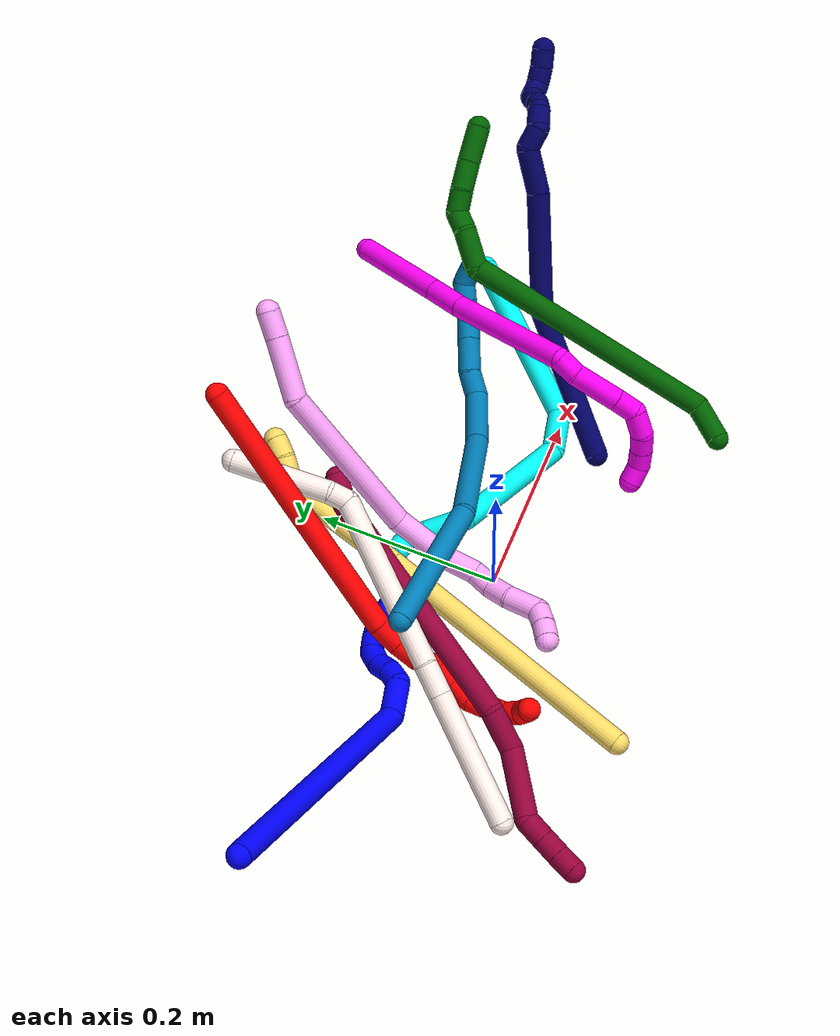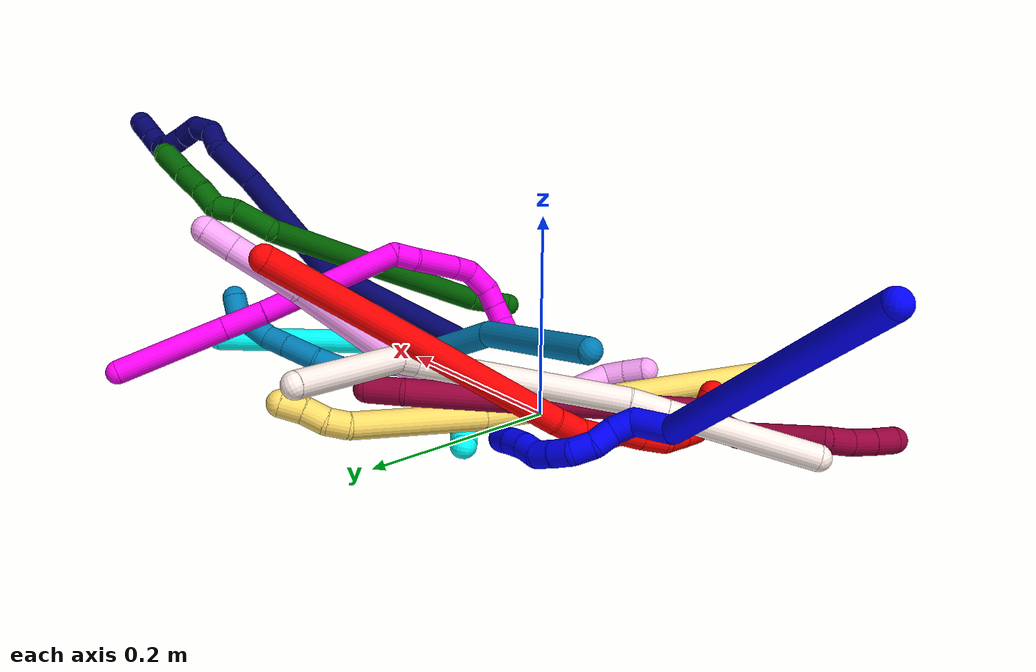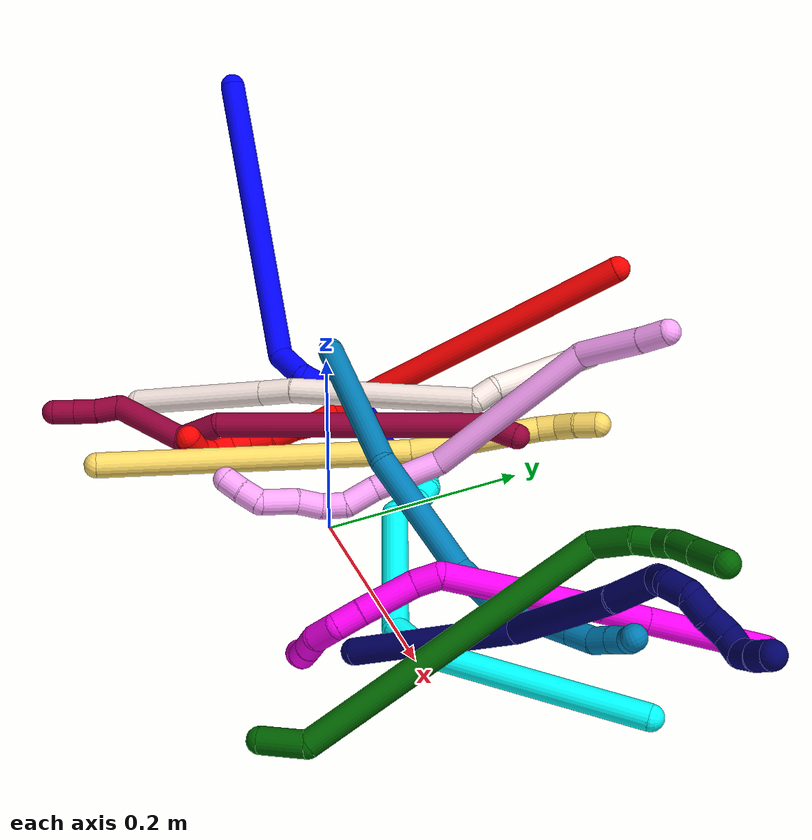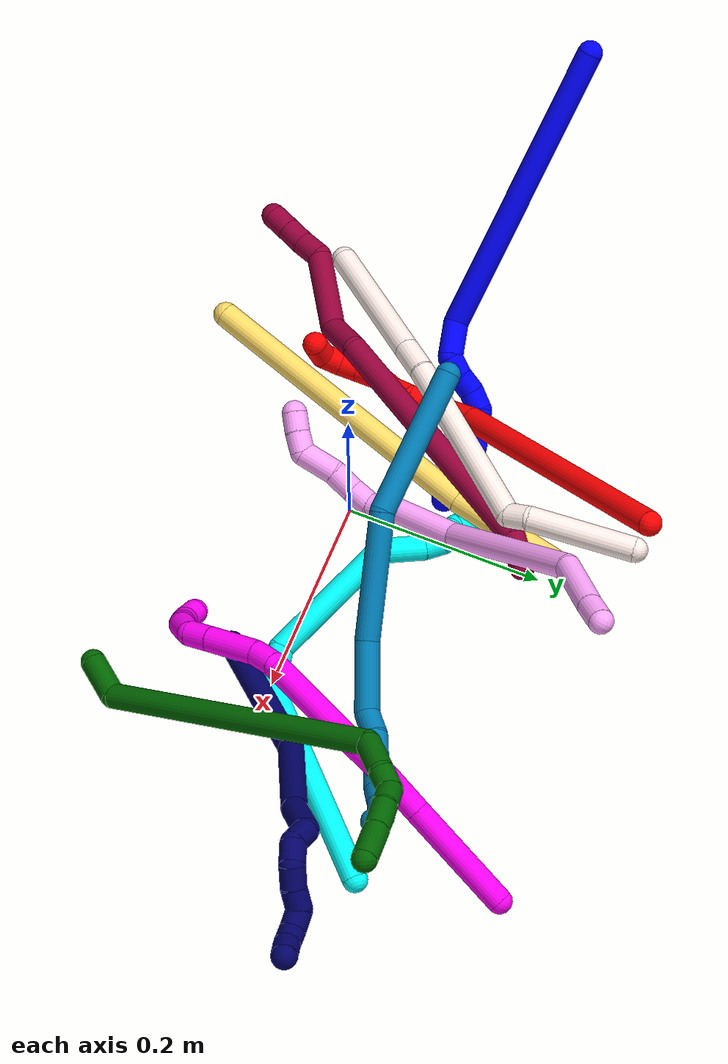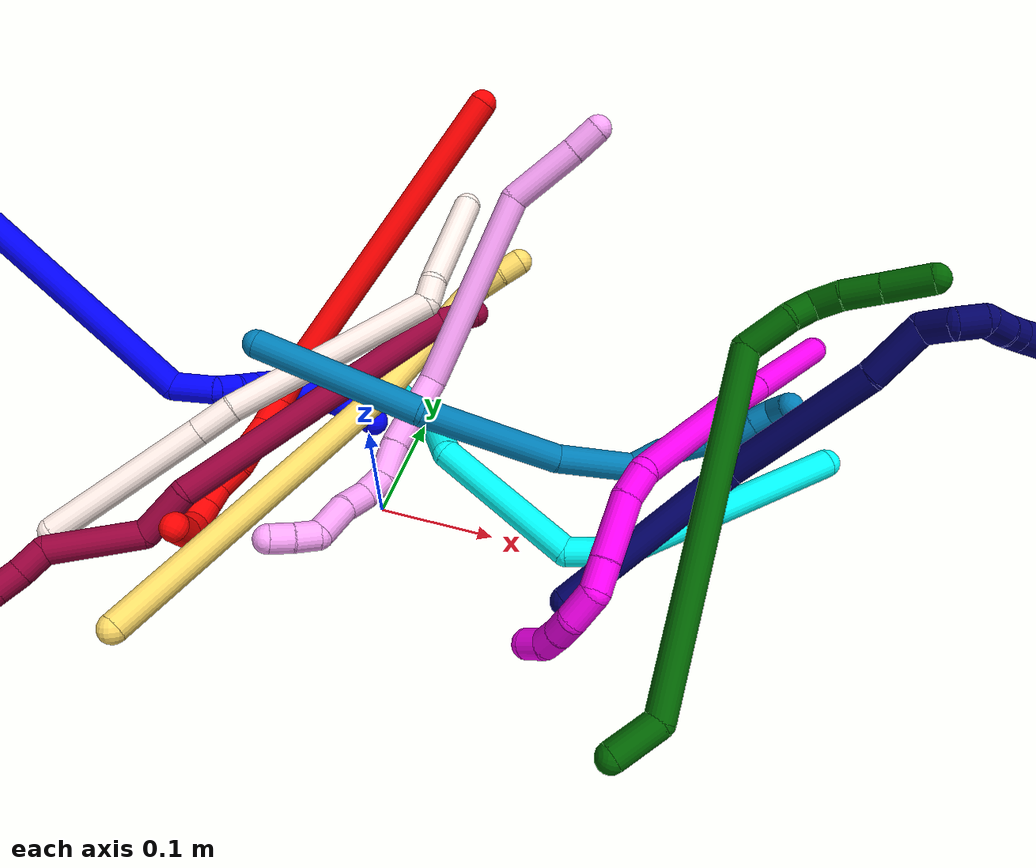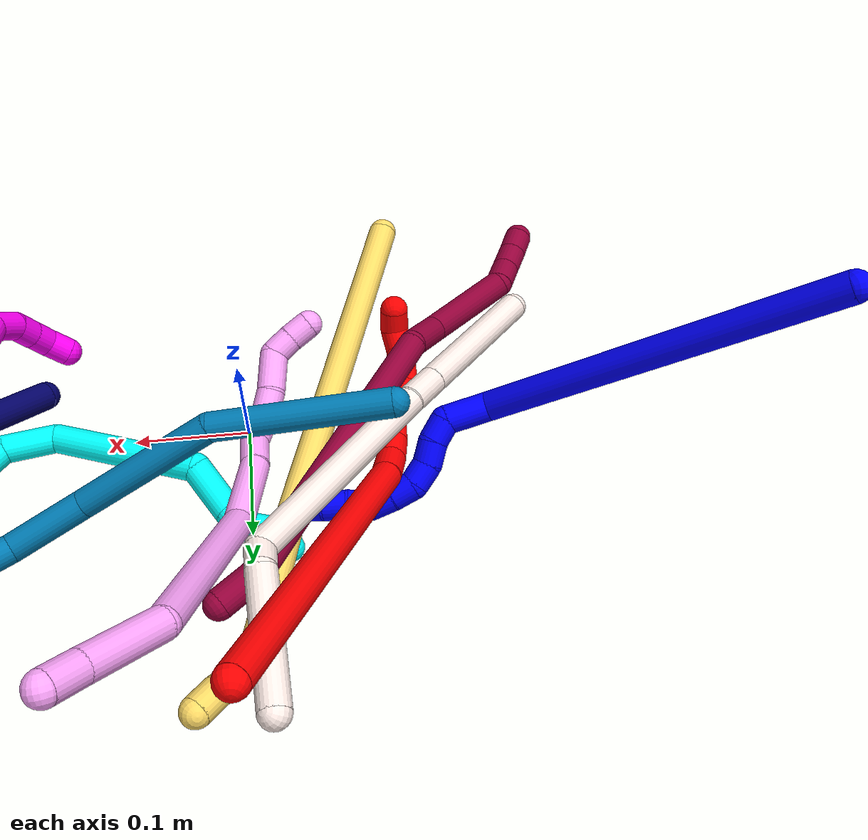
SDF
<sdf version="1.7">
 <world name="default">
  <plugin name="TubeGeneratorPlugin" filename="libtube_generator_plugin.so"/>
  <model name="photoneo_s_sensor">
   <static>1</static>
   <pose>0 0 2 1.57079 1.57079 3.14159</pose>
   <link name="link">
    <inertial><mass>0.1</mass></inertial>
    <sensor name="sensor" type="depth">
     <update_rate>30</update_rate>
     <camera>
      <horizontal_fov>1.22</horizontal_fov>
      <image><width>1920</width><height>1200</height><format>B8G8R8</format></image>
      <clip><near>0.1</near><far>4</far></clip>
      <depth_camera><output>points</output></depth_camera>
     </camera>
     <plugin name="camera_plugin" filename="libgazebo_ros_depth_camera.so">
      <baseline>0.2</baseline>
      <alwaysOn>1</alwaysOn>
      <updateRate>0.0</updateRate>
      <cameraName>camera_ir</cameraName>
      <imageTopicName>/camera/color/image_raw</imageTopicName>
      <cameraInfoTopicName>/camera/color/camera_info</cameraInfoTopicName>
      <depthImageTopicName>/camera/depth/image_raw</depthImageTopicName>
      <depthImageCameraInfoTopicName>/camera/depth/camera_info</depthImageCameraInfoTopicName>
      <pointCloudTopicName>/camera/depth/points</pointCloudTopicName>
      <frameName>fr_optical</frameName>
      <pointCloudCutoff>0.1</pointCloudCutoff>
      <pointCloudCutoffMax>2.0</pointCloudCutoffMax>
      <distortionK1>0</distortionK1>
      <distortionK2>0</distortionK2>
      <distortionK3>0</distortionK3>
      <distortionT1>0</distortionT1>
      <distortionT2>0</distortionT2>
      <CxPrime>0</CxPrime>
      <Cx>0</Cx>
      <Cy>0</Cy>
      <focalLength>0</focalLength>
      <hackBaseline>0</hackBaseline>
     </plugin>
    </sensor>
   </link>
  </model>
  <gravity>0 0 -9.8</gravity>
  <magnetic_field>6e-06 2.3e-05 -4.2e-05</magnetic_field>
  <atmosphere type="adiabatic"/>
  <physics name="default_physics" default="0" type="ode">
   <max_step_size>0.003</max_step_size>
   <real_time_factor>1</real_time_factor>
   <real_time_update_rate>1000</real_time_update_rate>
   <max_contacts>10000</max_contacts>
   <ode>
    <solver>
     <type>quick</type>
     <iters>100</iters>
     <sor>1.3</sor>
     <use_dynamic_moi_rescaling>0</use_dynamic_moi_rescaling>
    </solver>
    <constraints>
     <contact_max_correcting_vel>0</contact_max_correcting_vel>
     <contact_surface_layer>0.001</contact_surface_layer>
     <cfm>0</cfm>
     <erp>0.2</erp>
    </constraints>
   </ode>
  </physics>
  <scene><ambient>0.4 0.4 0.4 1</ambient><background>0.7 0.7 0.7 1</background><shadows>0</shadows></scene>
  <audio><device>default</device></audio>
  <spherical_coordinates>
   <surface_model>EARTH_WGS84</surface_model>
   <latitude_deg>0</latitude_deg>
   <longitude_deg>0</longitude_deg>
   <elevation>0</elevation>
   <heading_deg>0</heading_deg>
  </spherical_coordinates>
  <model name="bin">
   <static>1</static>
   <link name="bottom">
    <collision name="collision-bottom">
     <pose>0 0 -0.01 0 -0 0</pose>
     <geometry><box><size>0.8 0.6 0.02</size></box></geometry>
     <surface>
      <friction><ode><mu>100</mu><mu2>100</mu2></ode></friction>
      <contact><collide_bitmask>65535</collide_bitmask></contact>
     </surface>
    </collision>
   </link>
   <link name="west_wall">
    <collision name="collision-west_wall">
     <pose>-0.41 0 0.1 0 -0 0</pose>
     <geometry><box><size>0.02 0.6 0.2</size></box></geometry>
     <surface>
      <friction><ode><mu>100</mu><mu2>100</mu2></ode></friction>
      <contact><collide_bitmask>65535</collide_bitmask></contact>
     </surface>
    </collision>
   </link>
   <link name="east_wall">
    <collision name="collision-east_wall">
     <pose>0.41 0 0.1 0 -0 0</pose>
     <geometry><box><size>0.02 0.6 0.2</size></box></geometry>
     <surface>
      <friction><ode><mu>100</mu><mu2>100</mu2></ode></friction>
      <contact><collide_bitmask>65535</collide_bitmask></contact>
     </surface>
    </collision>
   </link>
   <link name="south_wall">
    <collision name="collision-south_wall">
     <pose>0 -0.31 0.1 0 -0 0</pose>
     <geometry><box><size>0.8 0.02 0.2</size></box></geometry>
     <surface>
      <friction><ode><mu>100</mu><mu2>100</mu2></ode></friction>
      <contact><collide_bitmask>65535</collide_bitmask></contact>
     </surface>
    </collision>
   </link>
   <link name="north_wall">
    <collision name="collision-north_wall">
     <pose>0 0.31 0.1 0 -0 0</pose>
     <geometry><box><size>0.8 0.02 0.2</size></box></geometry>
     <surface>
      <friction><ode><mu>100</mu><mu2>100</mu2></ode></friction>
      <contact><collide_bitmask>65535</collide_bitmask></contact>
     </surface>
    </collision>
   </link>
  </model>
  <model name="1">
   <static>0</static>
   <link name="1">
    <collision name="collision-cylinder-e_1_1_4">
     <pose>0.099642 0.033256 -0.108377 -2.84386 0.721064 -2.38436</pose>
     <geometry><cylinder><radius>0.0125</radius><length>0.301861</length></cylinder></geometry>
     <surface>
      <friction><ode><mu>1.16</mu><mu2>1.16</mu2><slip1>0</slip1><slip2>0</slip2></ode></friction>
      <contact><ode><kp>1e+06</kp><kd>1</kd><max_vel>0</max_vel><min_depth>0.001</min_depth></ode></contact>
     </surface>
    </collision>
    <visual name="visual-cylinder-e_1_1_4">
     <pose>0.099642 0.033256 -0.108377 -2.84386 0.721064 -2.38436</pose>
     <geometry><cylinder><radius>0.0125</radius><length>0.301861</length></cylinder></geometry>
     <material><ambient>0 0 1 1</ambient></material>
    </visual>
    <collision name="collision-cylinder-e_2_4_5">
     <pose>0.200756 0.066205 -0.235702 3.12536 0.077501 2.72889</pose>
     <geometry><cylinder><radius>0.0125</radius><length>0.038016</length></cylinder></geometry>
     <surface>
      <friction><ode><mu>1.16</mu><mu2>1.16</mu2><slip1>0</slip1><slip2>0</slip2></ode></friction>
      <contact><ode><kp>1e+06</kp><kd>1</kd><max_vel>0</max_vel><min_depth>0.001</min_depth></ode></contact>
     </surface>
    </collision>
    <visual name="visual-cylinder-e_2_4_5">
     <pose>0.200756 0.066205 -0.235702 3.12536 0.077501 2.72889</pose>
     <geometry><cylinder><radius>0.0125</radius><length>0.038016</length></cylinder></geometry>
     <material><ambient>0 0 1 1</ambient></material>
    </visual>
    <collision name="collision-cylinder-e_3_5_6">
     <pose>0.20568 0.059668 -0.261686 2.41683 0.352125 0.877498</pose>
     <geometry><cylinder><radius>0.0125</radius><length>0.020023</length></cylinder></geometry>
     <surface>
      <friction><ode><mu>1.16</mu><mu2>1.16</mu2><slip1>0</slip1><slip2>0</slip2></ode></friction>
      <contact><ode><kp>1e+06</kp><kd>1</kd><max_vel>0</max_vel><min_depth>0.001</min_depth></ode></contact>
     </surface>
    </collision>
    <visual name="visual-cylinder-e_3_5_6">
     <pose>0.20568 0.059668 -0.261686 2.41683 0.352125 0.877498</pose>
     <geometry><cylinder><radius>0.0125</radius><length>0.020023</length></cylinder></geometry>
     <material><ambient>0 0 1 1</ambient></material>
    </visual>
    <collision name="collision-cylinder-e_4_6_7">
     <pose>0.213589 0.045854 -0.273549 2.1377 0.460124 0.80669</pose>
     <geometry><cylinder><radius>0.0125</radius><length>0.020069</length></cylinder></geometry>
     <surface>
      <friction><ode><mu>1.16</mu><mu2>1.16</mu2><slip1>0</slip1><slip2>0</slip2></ode></friction>
      <contact><ode><kp>1e+06</kp><kd>1</kd><max_vel>0</max_vel><min_depth>0.001</min_depth></ode></contact>
     </surface>
    </collision>
    <visual name="visual-cylinder-e_4_6_7">
     <pose>0.213589 0.045854 -0.273549 2.1377 0.460124 0.80669</pose>
     <geometry><cylinder><radius>0.0125</radius><length>0.020069</length></cylinder></geometry>
     <material><ambient>0 0 1 1</ambient></material>
    </visual>
    <collision name="collision-cylinder-e_5_7_8">
     <pose>0.221045 0.03243 -0.285928 2.48332 0.3046 0.844664</pose>
     <geometry><cylinder><radius>0.0125</radius><length>0.020012</length></cylinder></geometry>
     <surface>
      <friction><ode><mu>1.16</mu><mu2>1.16</mu2><slip1>0</slip1><slip2>0</slip2></ode></friction>
      <contact><ode><kp>1e+06</kp><kd>1</kd><max_vel>0</max_vel><min_depth>0.001</min_depth></ode></contact>
     </surface>
    </collision>
    <visual name="visual-cylinder-e_5_7_8">
     <pose>0.221045 0.03243 -0.285928 2.48332 0.3046 0.844664</pose>
     <geometry><cylinder><radius>0.0125</radius><length>0.020012</length></cylinder></geometry>
     <material><ambient>0 0 1 1</ambient></material>
    </visual>
    <collision name="collision-cylinder-e_6_8_9">
     <pose>0.227448 0.025415 -0.302818 3.0164 0.346748 2.45424</pose>
     <geometry><cylinder><radius>0.0125</radius><length>0.020017</length></cylinder></geometry>
     <surface>
      <friction><ode><mu>1.16</mu><mu2>1.16</mu2><slip1>0</slip1><slip2>0</slip2></ode></friction>
      <contact><ode><kp>1e+06</kp><kd>1</kd><max_vel>0</max_vel><min_depth>0.001</min_depth></ode></contact>
     </surface>
    </collision>
    <visual name="visual-cylinder-e_6_8_9">
     <pose>0.227448 0.025415 -0.302818 3.0164 0.346748 2.45424</pose>
     <geometry><cylinder><radius>0.0125</radius><length>0.020017</length></cylinder></geometry>
     <material><ambient>0 0 1 1</ambient></material>
    </visual>
    <collision name="collision-cylinder-e_7_9_10">
     <pose>0.234321 0.024109 -0.321536 3.12766 0.354521 3.06387</pose>
     <geometry><cylinder><radius>0.0125</radius><length>0.020002</length></cylinder></geometry>
     <surface>
      <friction><ode><mu>1.16</mu><mu2>1.16</mu2><slip1>0</slip1><slip2>0</slip2></ode></friction>
      <contact><ode><kp>1e+06</kp><kd>1</kd><max_vel>0</max_vel><min_depth>0.001</min_depth></ode></contact>
     </surface>
    </collision>
    <visual name="visual-cylinder-e_7_9_10">
     <pose>0.234321 0.024109 -0.321536 3.12766 0.354521 3.06387</pose>
     <geometry><cylinder><radius>0.0125</radius><length>0.020002</length></cylinder></geometry>
     <material><ambient>0 0 1 1</ambient></material>
    </visual>
    <collision name="collision-cylinder-e_8_10_11">
     <pose>0.238072 0.027465 -0.340283 -2.78532 0.027963 -0.155014</pose>
     <geometry><cylinder><radius>0.0125</radius><length>0.02</length></cylinder></geometry>
     <surface>
      <friction><ode><mu>1.16</mu><mu2>1.16</mu2><slip1>0</slip1><slip2>0</slip2></ode></friction>
      <contact><ode><kp>1e+06</kp><kd>1</kd><max_vel>0</max_vel><min_depth>0.001</min_depth></ode></contact>
     </surface>
    </collision>
    <visual name="visual-cylinder-e_8_10_11">
     <pose>0.238072 0.027465 -0.340283 -2.78532 0.027963 -0.155014</pose>
     <geometry><cylinder><radius>0.0125</radius><length>0.02</length></cylinder></geometry>
     <material><ambient>0 0 1 1</ambient></material>
    </visual>
    <collision name="collision-cylinder-e_9_11_12">
     <pose>0.240265 0.033711 -0.359071 -2.85666 0.192472 -1.18474</pose>
     <geometry><cylinder><radius>0.0125</radius><length>0.02</length></cylinder></geometry>
     <surface>
      <friction><ode><mu>1.16</mu><mu2>1.16</mu2><slip1>0</slip1><slip2>0</slip2></ode></friction>
      <contact><ode><kp>1e+06</kp><kd>1</kd><max_vel>0</max_vel><min_depth>0.001</min_depth></ode></contact>
     </surface>
    </collision>
    <visual name="visual-cylinder-e_9_11_12">
     <pose>0.240265 0.033711 -0.359071 -2.85666 0.192472 -1.18474</pose>
     <geometry><cylinder><radius>0.0125</radius><length>0.02</length></cylinder></geometry>
     <material><ambient>0 0 1 1</ambient></material>
    </visual>
    <collision name="collision-cylinder-e_10_12_2">
     <pose>0.245589 0.04013 -0.377149 -2.7416 0.34809 -1.42901</pose>
     <geometry><cylinder><radius>0.0125</radius><length>0.02</length></cylinder></geometry>
     <surface>
      <friction><ode><mu>1.16</mu><mu2>1.16</mu2><slip1>0</slip1><slip2>0</slip2></ode></friction>
      <contact><ode><kp>1e+06</kp><kd>1</kd><max_vel>0</max_vel><min_depth>0.001</min_depth></ode></contact>
     </surface>
    </collision>
    <visual name="visual-cylinder-e_10_12_2">
     <pose>0.245589 0.04013 -0.377149 -2.7416 0.34809 -1.42901</pose>
     <geometry><cylinder><radius>0.0125</radius><length>0.02</length></cylinder></geometry>
     <material><ambient>0 0 1 1</ambient></material>
    </visual>
    <collision name="collision-sphere-2">
     <pose>0.249 0.043791 -0.385807 0 -0 0</pose>
     <geometry><sphere><radius>0.0125</radius></sphere></geometry>
     <surface>
      <friction><ode><mu>1.16</mu><mu2>1.16</mu2><slip1>0</slip1><slip2>0</slip2></ode></friction>
      <contact><ode><kp>1e+06</kp><kd>1</kd><max_vel>0</max_vel><min_depth>0.001</min_depth></ode></contact>
     </surface>
    </collision>
    <visual name="visual-sphere-2">
     <pose>0.249 0.043791 -0.385807 0 -0 0</pose>
     <geometry><sphere><radius>0.0125</radius></sphere></geometry>
     <material><ambient>0 0 1 1</ambient></material>
    </visual>
    <collision name="collision-sphere-12">
     <pose>0.242178 0.03647 -0.36849 0 -0 0</pose>
     <geometry><sphere><radius>0.0125</radius></sphere></geometry>
     <surface>
      <friction><ode><mu>1.16</mu><mu2>1.16</mu2><slip1>0</slip1><slip2>0</slip2></ode></friction>
      <contact><ode><kp>1e+06</kp><kd>1</kd><max_vel>0</max_vel><min_depth>0.001</min_depth></ode></contact>
     </surface>
    </collision>
    <visual name="visual-sphere-12">
     <pose>0.242178 0.03647 -0.36849 0 -0 0</pose>
     <geometry><sphere><radius>0.0125</radius></sphere></geometry>
     <material><ambient>0 0 1 1</ambient></material>
    </visual>
    <collision name="collision-sphere-11">
     <pose>0.238352 0.030952 -0.349651 0 -0 0</pose>
     <geometry><sphere><radius>0.0125</radius></sphere></geometry>
     <surface>
      <friction><ode><mu>1.16</mu><mu2>1.16</mu2><slip1>0</slip1><slip2>0</slip2></ode></friction>
      <contact><ode><kp>1e+06</kp><kd>1</kd><max_vel>0</max_vel><min_depth>0.001</min_depth></ode></contact>
     </surface>
    </collision>
    <visual name="visual-sphere-11">
     <pose>0.238352 0.030952 -0.349651 0 -0 0</pose>
     <geometry><sphere><radius>0.0125</radius></sphere></geometry>
     <material><ambient>0 0 1 1</ambient></material>
    </visual>
    <collision name="collision-sphere-10">
     <pose>0.237793 0.023979 -0.330914 0 -0 0</pose>
     <geometry><sphere><radius>0.0125</radius></sphere></geometry>
     <surface>
      <friction><ode><mu>1.16</mu><mu2>1.16</mu2><slip1>0</slip1><slip2>0</slip2></ode></friction>
      <contact><ode><kp>1e+06</kp><kd>1</kd><max_vel>0</max_vel><min_depth>0.001</min_depth></ode></contact>
     </surface>
    </collision>
    <visual name="visual-sphere-10">
     <pose>0.237793 0.023979 -0.330914 0 -0 0</pose>
     <geometry><sphere><radius>0.0125</radius></sphere></geometry>
     <material><ambient>0 0 1 1</ambient></material>
    </visual>
    <collision name="collision-sphere-9">
     <pose>0.230849 0.02424 -0.312158 0 -0 0</pose>
     <geometry><sphere><radius>0.0125</radius></sphere></geometry>
     <surface>
      <friction><ode><mu>1.16</mu><mu2>1.16</mu2><slip1>0</slip1><slip2>0</slip2></ode></friction>
      <contact><ode><kp>1e+06</kp><kd>1</kd><max_vel>0</max_vel><min_depth>0.001</min_depth></ode></contact>
     </surface>
    </collision>
    <visual name="visual-sphere-9">
     <pose>0.230849 0.02424 -0.312158 0 -0 0</pose>
     <geometry><sphere><radius>0.0125</radius></sphere></geometry>
     <material><ambient>0 0 1 1</ambient></material>
    </visual>
    <collision name="collision-sphere-4">
     <pose>0.199284 0.066513 -0.216754 0 -0 0</pose>
     <geometry><sphere><radius>0.0125</radius></sphere></geometry>
     <surface>
      <friction><ode><mu>1.16</mu><mu2>1.16</mu2><slip1>0</slip1><slip2>0</slip2></ode></friction>
      <contact><ode><kp>1e+06</kp><kd>1</kd><max_vel>0</max_vel><min_depth>0.001</min_depth></ode></contact>
     </surface>
    </collision>
    <visual name="visual-sphere-4">
     <pose>0.199284 0.066513 -0.216754 0 -0 0</pose>
     <geometry><sphere><radius>0.0125</radius></sphere></geometry>
     <material><ambient>0 0 1 1</ambient></material>
    </visual>
    <collision name="collision-sphere-1">
     <geometry><sphere><radius>0.0125</radius></sphere></geometry>
     <surface>
      <friction><ode><mu>1.16</mu><mu2>1.16</mu2><slip1>0</slip1><slip2>0</slip2></ode></friction>
      <contact><ode><kp>1e+06</kp><kd>1</kd><max_vel>0</max_vel><min_depth>0.001</min_depth></ode></contact>
     </surface>
    </collision>
    <visual name="visual-sphere-1">
     <geometry><sphere><radius>0.0125</radius></sphere></geometry>
     <material><ambient>0 0 1 1</ambient></material>
    </visual>
    <collision name="collision-sphere-8">
     <pose>0.224046 0.026591 -0.293479 0 -0 0</pose>
     <geometry><sphere><radius>0.0125</radius></sphere></geometry>
     <surface>
      <friction><ode><mu>1.16</mu><mu2>1.16</mu2><slip1>0</slip1><slip2>0</slip2></ode></friction>
      <contact><ode><kp>1e+06</kp><kd>1</kd><max_vel>0</max_vel><min_depth>0.001</min_depth></ode></contact>
     </surface>
    </collision>
    <visual name="visual-sphere-8">
     <pose>0.224046 0.026591 -0.293479 0 -0 0</pose>
     <geometry><sphere><radius>0.0125</radius></sphere></geometry>
     <material><ambient>0 0 1 1</ambient></material>
    </visual>
    <collision name="collision-sphere-5">
     <pose>0.202227 0.065897 -0.254651 0 -0 0</pose>
     <geometry><sphere><radius>0.0125</radius></sphere></geometry>
     <surface>
      <friction><ode><mu>1.16</mu><mu2>1.16</mu2><slip1>0</slip1><slip2>0</slip2></ode></friction>
      <contact><ode><kp>1e+06</kp><kd>1</kd><max_vel>0</max_vel><min_depth>0.001</min_depth></ode></contact>
     </surface>
    </collision>
    <visual name="visual-sphere-5">
     <pose>0.202227 0.065897 -0.254651 0 -0 0</pose>
     <geometry><sphere><radius>0.0125</radius></sphere></geometry>
     <material><ambient>0 0 1 1</ambient></material>
    </visual>
    <collision name="collision-sphere-6">
     <pose>0.209133 0.053438 -0.268721 0 -0 0</pose>
     <geometry><sphere><radius>0.0125</radius></sphere></geometry>
     <surface>
      <friction><ode><mu>1.16</mu><mu2>1.16</mu2><slip1>0</slip1><slip2>0</slip2></ode></friction>
      <contact><ode><kp>1e+06</kp><kd>1</kd><max_vel>0</max_vel><min_depth>0.001</min_depth></ode></contact>
     </surface>
    </collision>
    <visual name="visual-sphere-6">
     <pose>0.209133 0.053438 -0.268721 0 -0 0</pose>
     <geometry><sphere><radius>0.0125</radius></sphere></geometry>
     <material><ambient>0 0 1 1</ambient></material>
    </visual>
    <collision name="collision-sphere-7">
     <pose>0.218045 0.038269 -0.278378 0 -0 0</pose>
     <geometry><sphere><radius>0.0125</radius></sphere></geometry>
     <surface>
      <friction><ode><mu>1.16</mu><mu2>1.16</mu2><slip1>0</slip1><slip2>0</slip2></ode></friction>
      <contact><ode><kp>1e+06</kp><kd>1</kd><max_vel>0</max_vel><min_depth>0.001</min_depth></ode></contact>
     </surface>
    </collision>
    <visual name="visual-sphere-7">
     <pose>0.218045 0.038269 -0.278378 0 -0 0</pose>
     <geometry><sphere><radius>0.0125</radius></sphere></geometry>
     <material><ambient>0 0 1 1</ambient></material>
    </visual>
    <inertial>
     <pose>0.148513 0.036673 -0.184299 0 -0 0</pose>
     <mass>0.5</mass>
     <inertia>
      <ixx>-0.002426</ixx>
      <ixy>0</ixy>
      <ixz>0</ixz>
      <iyy>0.000731</iyy>
      <iyz>0</iyz>
      <izz>-0.002061</izz>
     </inertia>
    </inertial>
   </link>
   <pose>-0.439238 0.074641 0.245249 1.67638 1.42191 -1.24137</pose>
  </model>
  <model name="2">
   <static>0</static>
   <link name="2">
    <collision name="collision-cylinder-e_1_1_4">
     <pose>-0.052993 -0.046539 -0.128684 2.79457 -0.369477 -1.63482</pose>
     <geometry><cylinder><radius>0.0125</radius><length>0.293489</length></cylinder></geometry>
     <surface>
      <friction><ode><mu>1.16</mu><mu2>1.16</mu2><slip1>0</slip1><slip2>0</slip2></ode></friction>
      <contact><ode><kp>1e+06</kp><kd>1</kd><max_vel>0</max_vel><min_depth>0.001</min_depth></ode></contact>
     </surface>
    </collision>
    <visual name="visual-cylinder-e_1_1_4">
     <pose>-0.052993 -0.046539 -0.128684 2.79457 -0.369477 -1.63482</pose>
     <geometry><cylinder><radius>0.0125</radius><length>0.293489</length></cylinder></geometry>
     <material><ambient>1 0 0 1</ambient></material>
    </visual>
    <collision name="collision-cylinder-e_2_4_5">
     <pose>-0.110572 -0.095265 -0.27073 2.9794 -0.326565 -2.22502</pose>
     <geometry><cylinder><radius>0.0125</radius><length>0.028588</length></cylinder></geometry>
     <surface>
      <friction><ode><mu>1.16</mu><mu2>1.16</mu2><slip1>0</slip1><slip2>0</slip2></ode></friction>
      <contact><ode><kp>1e+06</kp><kd>1</kd><max_vel>0</max_vel><min_depth>0.001</min_depth></ode></contact>
     </surface>
    </collision>
    <visual name="visual-cylinder-e_2_4_5">
     <pose>-0.110572 -0.095265 -0.27073 2.9794 -0.326565 -2.22502</pose>
     <geometry><cylinder><radius>0.0125</radius><length>0.028588</length></cylinder></geometry>
     <material><ambient>1 0 0 1</ambient></material>
    </visual>
    <collision name="collision-cylinder-e_3_5_6">
     <pose>-0.117473 -0.098651 -0.296977 3.04875 -0.177037 -2.17718</pose>
     <geometry><cylinder><radius>0.0125</radius><length>0.026295</length></cylinder></geometry>
     <surface>
      <friction><ode><mu>1.16</mu><mu2>1.16</mu2><slip1>0</slip1><slip2>0</slip2></ode></friction>
      <contact><ode><kp>1e+06</kp><kd>1</kd><max_vel>0</max_vel><min_depth>0.001</min_depth></ode></contact>
     </surface>
    </collision>
    <visual name="visual-cylinder-e_3_5_6">
     <pose>-0.117473 -0.098651 -0.296977 3.04875 -0.177037 -2.17718</pose>
     <geometry><cylinder><radius>0.0125</radius><length>0.026295</length></cylinder></geometry>
     <material><ambient>1 0 0 1</ambient></material>
    </visual>
    <collision name="collision-cylinder-e_4_6_7">
     <pose>-0.116904 -0.099991 -0.321336 3.12934 0.246355 3.04266</pose>
     <geometry><cylinder><radius>0.0125</radius><length>0.023661</length></cylinder></geometry>
     <surface>
      <friction><ode><mu>1.16</mu><mu2>1.16</mu2><slip1>0</slip1><slip2>0</slip2></ode></friction>
      <contact><ode><kp>1e+06</kp><kd>1</kd><max_vel>0</max_vel><min_depth>0.001</min_depth></ode></contact>
     </surface>
    </collision>
    <visual name="visual-cylinder-e_4_6_7">
     <pose>-0.116904 -0.099991 -0.321336 3.12934 0.246355 3.04266</pose>
     <geometry><cylinder><radius>0.0125</radius><length>0.023661</length></cylinder></geometry>
     <material><ambient>1 0 0 1</ambient></material>
    </visual>
    <collision name="collision-cylinder-e_5_7_8">
     <pose>-0.115809 -0.101871 -0.343699 2.98324 -0.160958 -1.58719</pose>
     <geometry><cylinder><radius>0.0125</radius><length>0.022346</length></cylinder></geometry>
     <surface>
      <friction><ode><mu>1.16</mu><mu2>1.16</mu2><slip1>0</slip1><slip2>0</slip2></ode></friction>
      <contact><ode><kp>1e+06</kp><kd>1</kd><max_vel>0</max_vel><min_depth>0.001</min_depth></ode></contact>
     </surface>
    </collision>
    <visual name="visual-cylinder-e_5_7_8">
     <pose>-0.115809 -0.101871 -0.343699 2.98324 -0.160958 -1.58719</pose>
     <geometry><cylinder><radius>0.0125</radius><length>0.022346</length></cylinder></geometry>
     <material><ambient>1 0 0 1</ambient></material>
    </visual>
    <collision name="collision-cylinder-e_6_8_9">
     <pose>-0.118097 -0.108116 -0.366169 2.7705 -0.040027 -0.212467</pose>
     <geometry><cylinder><radius>0.0125</radius><length>0.024869</length></cylinder></geometry>
     <surface>
      <friction><ode><mu>1.16</mu><mu2>1.16</mu2><slip1>0</slip1><slip2>0</slip2></ode></friction>
      <contact><ode><kp>1e+06</kp><kd>1</kd><max_vel>0</max_vel><min_depth>0.001</min_depth></ode></contact>
     </surface>
    </collision>
    <visual name="visual-cylinder-e_6_8_9">
     <pose>-0.118097 -0.108116 -0.366169 2.7705 -0.040027 -0.212467</pose>
     <geometry><cylinder><radius>0.0125</radius><length>0.024869</length></cylinder></geometry>
     <material><ambient>1 0 0 1</ambient></material>
    </visual>
    <collision name="collision-cylinder-e_7_9_10">
     <pose>-0.116472 -0.112222 -0.387714 -3.10157 0.209714 -2.76579</pose>
     <geometry><cylinder><radius>0.0125</radius><length>0.020396</length></cylinder></geometry>
     <surface>
      <friction><ode><mu>1.16</mu><mu2>1.16</mu2><slip1>0</slip1><slip2>0</slip2></ode></friction>
      <contact><ode><kp>1e+06</kp><kd>1</kd><max_vel>0</max_vel><min_depth>0.001</min_depth></ode></contact>
     </surface>
    </collision>
    <visual name="visual-cylinder-e_7_9_10">
     <pose>-0.116472 -0.112222 -0.387714 -3.10157 0.209714 -2.76579</pose>
     <geometry><cylinder><radius>0.0125</radius><length>0.020396</length></cylinder></geometry>
     <material><ambient>1 0 0 1</ambient></material>
    </visual>
    <collision name="collision-cylinder-e_8_10_11">
     <pose>-0.112043 -0.111255 -0.407563 -3.08411 0.228844 -2.65137</pose>
     <geometry><cylinder><radius>0.0125</radius><length>0.020327</length></cylinder></geometry>
     <surface>
      <friction><ode><mu>1.16</mu><mu2>1.16</mu2><slip1>0</slip1><slip2>0</slip2></ode></friction>
      <contact><ode><kp>1e+06</kp><kd>1</kd><max_vel>0</max_vel><min_depth>0.001</min_depth></ode></contact>
     </surface>
    </collision>
    <visual name="visual-cylinder-e_8_10_11">
     <pose>-0.112043 -0.111255 -0.407563 -3.08411 0.228844 -2.65137</pose>
     <geometry><cylinder><radius>0.0125</radius><length>0.020327</length></cylinder></geometry>
     <material><ambient>1 0 0 1</ambient></material>
    </visual>
    <collision name="collision-cylinder-e_9_11_12">
     <pose>-0.102387 -0.108497 -0.423866 -2.81303 0.825465 -2.41777</pose>
     <geometry><cylinder><radius>0.0125</radius><length>0.020004</length></cylinder></geometry>
     <surface>
      <friction><ode><mu>1.16</mu><mu2>1.16</mu2><slip1>0</slip1><slip2>0</slip2></ode></friction>
      <contact><ode><kp>1e+06</kp><kd>1</kd><max_vel>0</max_vel><min_depth>0.001</min_depth></ode></contact>
     </surface>
    </collision>
    <visual name="visual-cylinder-e_9_11_12">
     <pose>-0.102387 -0.108497 -0.423866 -2.81303 0.825465 -2.41777</pose>
     <geometry><cylinder><radius>0.0125</radius><length>0.020004</length></cylinder></geometry>
     <material><ambient>1 0 0 1</ambient></material>
    </visual>
    <collision name="collision-cylinder-e_10_12_2">
     <pose>-0.085213 -0.106596 -0.432193 2.99145 1.37704 2.95928</pose>
     <geometry><cylinder><radius>0.0125</radius><length>0.020024</length></cylinder></geometry>
     <surface>
      <friction><ode><mu>1.16</mu><mu2>1.16</mu2><slip1>0</slip1><slip2>0</slip2></ode></friction>
      <contact><ode><kp>1e+06</kp><kd>1</kd><max_vel>0</max_vel><min_depth>0.001</min_depth></ode></contact>
     </surface>
    </collision>
    <visual name="visual-cylinder-e_10_12_2">
     <pose>-0.085213 -0.106596 -0.432193 2.99145 1.37704 2.95928</pose>
     <geometry><cylinder><radius>0.0125</radius><length>0.020024</length></cylinder></geometry>
     <material><ambient>1 0 0 1</ambient></material>
    </visual>
    <collision name="collision-sphere-2">
     <pose>-0.075388 -0.106885 -0.434099 0 -0 0</pose>
     <geometry><sphere><radius>0.0125</radius></sphere></geometry>
     <surface>
      <friction><ode><mu>1.16</mu><mu2>1.16</mu2><slip1>0</slip1><slip2>0</slip2></ode></friction>
      <contact><ode><kp>1e+06</kp><kd>1</kd><max_vel>0</max_vel><min_depth>0.001</min_depth></ode></contact>
     </surface>
    </collision>
    <visual name="visual-sphere-2">
     <pose>-0.075388 -0.106885 -0.434099 0 -0 0</pose>
     <geometry><sphere><radius>0.0125</radius></sphere></geometry>
     <material><ambient>1 0 0 1</ambient></material>
    </visual>
    <collision name="collision-sphere-12">
     <pose>-0.095037 -0.106308 -0.430287 0 -0 0</pose>
     <geometry><sphere><radius>0.0125</radius></sphere></geometry>
     <surface>
      <friction><ode><mu>1.16</mu><mu2>1.16</mu2><slip1>0</slip1><slip2>0</slip2></ode></friction>
      <contact><ode><kp>1e+06</kp><kd>1</kd><max_vel>0</max_vel><min_depth>0.001</min_depth></ode></contact>
     </surface>
    </collision>
    <visual name="visual-sphere-12">
     <pose>-0.095037 -0.106308 -0.430287 0 -0 0</pose>
     <geometry><sphere><radius>0.0125</radius></sphere></geometry>
     <material><ambient>1 0 0 1</ambient></material>
    </visual>
    <collision name="collision-sphere-11">
     <pose>-0.109738 -0.110686 -0.417445 0 -0 0</pose>
     <geometry><sphere><radius>0.0125</radius></sphere></geometry>
     <surface>
      <friction><ode><mu>1.16</mu><mu2>1.16</mu2><slip1>0</slip1><slip2>0</slip2></ode></friction>
      <contact><ode><kp>1e+06</kp><kd>1</kd><max_vel>0</max_vel><min_depth>0.001</min_depth></ode></contact>
     </surface>
    </collision>
    <visual name="visual-sphere-11">
     <pose>-0.109738 -0.110686 -0.417445 0 -0 0</pose>
     <geometry><sphere><radius>0.0125</radius></sphere></geometry>
     <material><ambient>1 0 0 1</ambient></material>
    </visual>
    <collision name="collision-sphere-10">
     <pose>-0.114349 -0.111823 -0.397681 0 -0 0</pose>
     <geometry><sphere><radius>0.0125</radius></sphere></geometry>
     <surface>
      <friction><ode><mu>1.16</mu><mu2>1.16</mu2><slip1>0</slip1><slip2>0</slip2></ode></friction>
      <contact><ode><kp>1e+06</kp><kd>1</kd><max_vel>0</max_vel><min_depth>0.001</min_depth></ode></contact>
     </surface>
    </collision>
    <visual name="visual-sphere-10">
     <pose>-0.114349 -0.111823 -0.397681 0 -0 0</pose>
     <geometry><sphere><radius>0.0125</radius></sphere></geometry>
     <material><ambient>1 0 0 1</ambient></material>
    </visual>
    <collision name="collision-sphere-9">
     <pose>-0.118595 -0.112621 -0.377748 0 -0 0</pose>
     <geometry><sphere><radius>0.0125</radius></sphere></geometry>
     <surface>
      <friction><ode><mu>1.16</mu><mu2>1.16</mu2><slip1>0</slip1><slip2>0</slip2></ode></friction>
      <contact><ode><kp>1e+06</kp><kd>1</kd><max_vel>0</max_vel><min_depth>0.001</min_depth></ode></contact>
     </surface>
    </collision>
    <visual name="visual-sphere-9">
     <pose>-0.118595 -0.112621 -0.377748 0 -0 0</pose>
     <geometry><sphere><radius>0.0125</radius></sphere></geometry>
     <material><ambient>1 0 0 1</ambient></material>
    </visual>
    <collision name="collision-sphere-4">
     <pose>-0.105987 -0.093078 -0.257369 0 -0 0</pose>
     <geometry><sphere><radius>0.0125</radius></sphere></geometry>
     <surface>
      <friction><ode><mu>1.16</mu><mu2>1.16</mu2><slip1>0</slip1><slip2>0</slip2></ode></friction>
      <contact><ode><kp>1e+06</kp><kd>1</kd><max_vel>0</max_vel><min_depth>0.001</min_depth></ode></contact>
     </surface>
    </collision>
    <visual name="visual-sphere-4">
     <pose>-0.105987 -0.093078 -0.257369 0 -0 0</pose>
     <geometry><sphere><radius>0.0125</radius></sphere></geometry>
     <material><ambient>1 0 0 1</ambient></material>
    </visual>
    <collision name="collision-sphere-1">
     <geometry><sphere><radius>0.0125</radius></sphere></geometry>
     <surface>
      <friction><ode><mu>1.16</mu><mu2>1.16</mu2><slip1>0</slip1><slip2>0</slip2></ode></friction>
      <contact><ode><kp>1e+06</kp><kd>1</kd><max_vel>0</max_vel><min_depth>0.001</min_depth></ode></contact>
     </surface>
    </collision>
    <visual name="visual-sphere-1">
     <geometry><sphere><radius>0.0125</radius></sphere></geometry>
     <material><ambient>1 0 0 1</ambient></material>
    </visual>
    <collision name="collision-sphere-8">
     <pose>-0.1176 -0.10361 -0.35459 0 -0 0</pose>
     <geometry><sphere><radius>0.0125</radius></sphere></geometry>
     <surface>
      <friction><ode><mu>1.16</mu><mu2>1.16</mu2><slip1>0</slip1><slip2>0</slip2></ode></friction>
      <contact><ode><kp>1e+06</kp><kd>1</kd><max_vel>0</max_vel><min_depth>0.001</min_depth></ode></contact>
     </surface>
    </collision>
    <visual name="visual-sphere-8">
     <pose>-0.1176 -0.10361 -0.35459 0 -0 0</pose>
     <geometry><sphere><radius>0.0125</radius></sphere></geometry>
     <material><ambient>1 0 0 1</ambient></material>
    </visual>
    <collision name="collision-sphere-5">
     <pose>-0.115158 -0.097451 -0.284091 0 -0 0</pose>
     <geometry><sphere><radius>0.0125</radius></sphere></geometry>
     <surface>
      <friction><ode><mu>1.16</mu><mu2>1.16</mu2><slip1>0</slip1><slip2>0</slip2></ode></friction>
      <contact><ode><kp>1e+06</kp><kd>1</kd><max_vel>0</max_vel><min_depth>0.001</min_depth></ode></contact>
     </surface>
    </collision>
    <visual name="visual-sphere-5">
     <pose>-0.115158 -0.097451 -0.284091 0 -0 0</pose>
     <geometry><sphere><radius>0.0125</radius></sphere></geometry>
     <material><ambient>1 0 0 1</ambient></material>
    </visual>
    <collision name="collision-sphere-6">
     <pose>-0.119789 -0.09985 -0.309863 0 -0 0</pose>
     <geometry><sphere><radius>0.0125</radius></sphere></geometry>
     <surface>
      <friction><ode><mu>1.16</mu><mu2>1.16</mu2><slip1>0</slip1><slip2>0</slip2></ode></friction>
      <contact><ode><kp>1e+06</kp><kd>1</kd><max_vel>0</max_vel><min_depth>0.001</min_depth></ode></contact>
     </surface>
    </collision>
    <visual name="visual-sphere-6">
     <pose>-0.119789 -0.09985 -0.309863 0 -0 0</pose>
     <geometry><sphere><radius>0.0125</radius></sphere></geometry>
     <material><ambient>1 0 0 1</ambient></material>
    </visual>
    <collision name="collision-sphere-7">
     <pose>-0.114018 -0.100132 -0.332808 0 -0 0</pose>
     <geometry><sphere><radius>0.0125</radius></sphere></geometry>
     <surface>
      <friction><ode><mu>1.16</mu><mu2>1.16</mu2><slip1>0</slip1><slip2>0</slip2></ode></friction>
      <contact><ode><kp>1e+06</kp><kd>1</kd><max_vel>0</max_vel><min_depth>0.001</min_depth></ode></contact>
     </surface>
    </collision>
    <visual name="visual-sphere-7">
     <pose>-0.114018 -0.100132 -0.332808 0 -0 0</pose>
     <geometry><sphere><radius>0.0125</radius></sphere></geometry>
     <material><ambient>1 0 0 1</ambient></material>
    </visual>
    <inertial>
     <pose>-0.077003 -0.070325 -0.222064 0 -0 0</pose>
     <mass>0.5</mass>
     <inertia>
      <ixx>-0.002118</ixx>
      <ixy>0</ixy>
      <ixz>0</ixz>
      <iyy>-0.001592</iyy>
      <iyz>0</iyz>
      <izz>0.001402</izz>
     </inertia>
    </inertial>
   </link>
   <pose>-0.004037 0.302473 0.217456 -0.105834 -1.32331 -1.52316</pose>
  </model>
  <model name="3">
   <static>0</static>
   <link name="3">
    <collision name="collision-cylinder-e_1_1_4">
     <pose>-0.011539 -0.014302 -0.103089 3.00373 -0.110418 -1.35009</pose>
     <geometry><cylinder><radius>0.0125</radius><length>0.209428</length></cylinder></geometry>
     <surface>
      <friction><ode><mu>1.16</mu><mu2>1.16</mu2><slip1>0</slip1><slip2>0</slip2></ode></friction>
      <contact><ode><kp>1e+06</kp><kd>1</kd><max_vel>0</max_vel><min_depth>0.001</min_depth></ode></contact>
     </surface>
    </collision>
    <visual name="visual-cylinder-e_1_1_4">
     <pose>-0.011539 -0.014302 -0.103089 3.00373 -0.110418 -1.35009</pose>
     <geometry><cylinder><radius>0.0125</radius><length>0.209428</length></cylinder></geometry>
     <material><ambient>0.003922 1 0.996078 1</ambient></material>
    </visual>
    <collision name="collision-cylinder-e_2_4_5">
     <pose>-0.03074 -0.02023 -0.225763 -2.73748 -0.345306 1.41049</pose>
     <geometry><cylinder><radius>0.0125</radius><length>0.045272</length></cylinder></geometry>
     <surface>
      <friction><ode><mu>1.16</mu><mu2>1.16</mu2><slip1>0</slip1><slip2>0</slip2></ode></friction>
      <contact><ode><kp>1e+06</kp><kd>1</kd><max_vel>0</max_vel><min_depth>0.001</min_depth></ode></contact>
     </surface>
    </collision>
    <visual name="visual-cylinder-e_2_4_5">
     <pose>-0.03074 -0.02023 -0.225763 -2.73748 -0.345306 1.41049</pose>
     <geometry><cylinder><radius>0.0125</radius><length>0.045272</length></cylinder></geometry>
     <material><ambient>0.003922 1 0.996078 1</ambient></material>
    </visual>
    <collision name="collision-cylinder-e_3_5_6">
     <pose>-0.0882 0.027448 -0.270565 -2.14128 -0.817523 1.34043</pose>
     <geometry><cylinder><radius>0.0125</radius><length>0.136536</length></cylinder></geometry>
     <surface>
      <friction><ode><mu>1.16</mu><mu2>1.16</mu2><slip1>0</slip1><slip2>0</slip2></ode></friction>
      <contact><ode><kp>1e+06</kp><kd>1</kd><max_vel>0</max_vel><min_depth>0.001</min_depth></ode></contact>
     </surface>
    </collision>
    <visual name="visual-cylinder-e_3_5_6">
     <pose>-0.0882 0.027448 -0.270565 -2.14128 -0.817523 1.34043</pose>
     <geometry><cylinder><radius>0.0125</radius><length>0.136536</length></cylinder></geometry>
     <material><ambient>0.003922 1 0.996078 1</ambient></material>
    </visual>
    <collision name="collision-cylinder-e_4_6_7">
     <pose>-0.145554 0.088384 -0.293825 -1.4805 -0.334723 0.306256</pose>
     <geometry><cylinder><radius>0.0125</radius><length>0.045997</length></cylinder></geometry>
     <surface>
      <friction><ode><mu>1.16</mu><mu2>1.16</mu2><slip1>0</slip1><slip2>0</slip2></ode></friction>
      <contact><ode><kp>1e+06</kp><kd>1</kd><max_vel>0</max_vel><min_depth>0.001</min_depth></ode></contact>
     </surface>
    </collision>
    <visual name="visual-cylinder-e_4_6_7">
     <pose>-0.145554 0.088384 -0.293825 -1.4805 -0.334723 0.306256</pose>
     <geometry><cylinder><radius>0.0125</radius><length>0.045997</length></cylinder></geometry>
     <material><ambient>0.003922 1 0.996078 1</ambient></material>
    </visual>
    <collision name="collision-cylinder-e_5_7_8">
     <pose>-0.15924 0.118027 -0.291442 -1.51782 -0.652643 0.621129</pose>
     <geometry><cylinder><radius>0.0125</radius><length>0.020192</length></cylinder></geometry>
     <surface>
      <friction><ode><mu>1.16</mu><mu2>1.16</mu2><slip1>0</slip1><slip2>0</slip2></ode></friction>
      <contact><ode><kp>1e+06</kp><kd>1</kd><max_vel>0</max_vel><min_depth>0.001</min_depth></ode></contact>
     </surface>
    </collision>
    <visual name="visual-cylinder-e_5_7_8">
     <pose>-0.15924 0.118027 -0.291442 -1.51782 -0.652643 0.621129</pose>
     <geometry><cylinder><radius>0.0125</radius><length>0.020192</length></cylinder></geometry>
     <material><ambient>0.003922 1 0.996078 1</ambient></material>
    </visual>
    <collision name="collision-cylinder-e_6_8_9">
     <pose>-0.17115 0.133122 -0.296772 -2.25296 -0.564395 1.09405</pose>
     <geometry><cylinder><radius>0.0125</radius><length>0.021606</length></cylinder></geometry>
     <surface>
      <friction><ode><mu>1.16</mu><mu2>1.16</mu2><slip1>0</slip1><slip2>0</slip2></ode></friction>
      <contact><ode><kp>1e+06</kp><kd>1</kd><max_vel>0</max_vel><min_depth>0.001</min_depth></ode></contact>
     </surface>
    </collision>
    <visual name="visual-cylinder-e_6_8_9">
     <pose>-0.17115 0.133122 -0.296772 -2.25296 -0.564395 1.09405</pose>
     <geometry><cylinder><radius>0.0125</radius><length>0.021606</length></cylinder></geometry>
     <material><ambient>0.003922 1 0.996078 1</ambient></material>
    </visual>
    <collision name="collision-cylinder-e_7_9_2">
     <pose>-0.180256 0.150011 -0.304177 -1.73756 -0.323005 0.380613</pose>
     <geometry><cylinder><radius>0.0125</radius><length>0.020968</length></cylinder></geometry>
     <surface>
      <friction><ode><mu>1.16</mu><mu2>1.16</mu2><slip1>0</slip1><slip2>0</slip2></ode></friction>
      <contact><ode><kp>1e+06</kp><kd>1</kd><max_vel>0</max_vel><min_depth>0.001</min_depth></ode></contact>
     </surface>
    </collision>
    <visual name="visual-cylinder-e_7_9_2">
     <pose>-0.180256 0.150011 -0.304177 -1.73756 -0.323005 0.380613</pose>
     <geometry><cylinder><radius>0.0125</radius><length>0.020968</length></cylinder></geometry>
     <material><ambient>0.003922 1 0.996078 1</ambient></material>
    </visual>
    <collision name="collision-sphere-2">
     <pose>-0.183584 0.159815 -0.305827 0 -0 0</pose>
     <geometry><sphere><radius>0.0125</radius></sphere></geometry>
     <surface>
      <friction><ode><mu>1.16</mu><mu2>1.16</mu2><slip1>0</slip1><slip2>0</slip2></ode></friction>
      <contact><ode><kp>1e+06</kp><kd>1</kd><max_vel>0</max_vel><min_depth>0.001</min_depth></ode></contact>
     </surface>
    </collision>
    <visual name="visual-sphere-2">
     <pose>-0.183584 0.159815 -0.305827 0 -0 0</pose>
     <geometry><sphere><radius>0.0125</radius></sphere></geometry>
     <material><ambient>0.003922 1 0.996078 1</ambient></material>
    </visual>
    <collision name="collision-sphere-9">
     <pose>-0.176929 0.140207 -0.302526 0 -0 0</pose>
     <geometry><sphere><radius>0.0125</radius></sphere></geometry>
     <surface>
      <friction><ode><mu>1.16</mu><mu2>1.16</mu2><slip1>0</slip1><slip2>0</slip2></ode></friction>
      <contact><ode><kp>1e+06</kp><kd>1</kd><max_vel>0</max_vel><min_depth>0.001</min_depth></ode></contact>
     </surface>
    </collision>
    <visual name="visual-sphere-9">
     <pose>-0.176929 0.140207 -0.302526 0 -0 0</pose>
     <geometry><sphere><radius>0.0125</radius></sphere></geometry>
     <material><ambient>0.003922 1 0.996078 1</ambient></material>
    </visual>
    <collision name="collision-sphere-4">
     <pose>-0.023078 -0.028605 -0.206178 0 -0 0</pose>
     <geometry><sphere><radius>0.0125</radius></sphere></geometry>
     <surface>
      <friction><ode><mu>1.16</mu><mu2>1.16</mu2><slip1>0</slip1><slip2>0</slip2></ode></friction>
      <contact><ode><kp>1e+06</kp><kd>1</kd><max_vel>0</max_vel><min_depth>0.001</min_depth></ode></contact>
     </surface>
    </collision>
    <visual name="visual-sphere-4">
     <pose>-0.023078 -0.028605 -0.206178 0 -0 0</pose>
     <geometry><sphere><radius>0.0125</radius></sphere></geometry>
     <material><ambient>0.003922 1 0.996078 1</ambient></material>
    </visual>
    <collision name="collision-sphere-1">
     <geometry><sphere><radius>0.0125</radius></sphere></geometry>
     <surface>
      <friction><ode><mu>1.16</mu><mu2>1.16</mu2><slip1>0</slip1><slip2>0</slip2></ode></friction>
      <contact><ode><kp>1e+06</kp><kd>1</kd><max_vel>0</max_vel><min_depth>0.001</min_depth></ode></contact>
     </surface>
    </collision>
    <visual name="visual-sphere-1">
     <geometry><sphere><radius>0.0125</radius></sphere></geometry>
     <material><ambient>0.003922 1 0.996078 1</ambient></material>
    </visual>
    <collision name="collision-sphere-8">
     <pose>-0.165371 0.126037 -0.291017 0 -0 0</pose>
     <geometry><sphere><radius>0.0125</radius></sphere></geometry>
     <surface>
      <friction><ode><mu>1.16</mu><mu2>1.16</mu2><slip1>0</slip1><slip2>0</slip2></ode></friction>
      <contact><ode><kp>1e+06</kp><kd>1</kd><max_vel>0</max_vel><min_depth>0.001</min_depth></ode></contact>
     </surface>
    </collision>
    <visual name="visual-sphere-8">
     <pose>-0.165371 0.126037 -0.291017 0 -0 0</pose>
     <geometry><sphere><radius>0.0125</radius></sphere></geometry>
     <material><ambient>0.003922 1 0.996078 1</ambient></material>
    </visual>
    <collision name="collision-sphere-5">
     <pose>-0.038402 -0.011854 -0.245347 0 -0 0</pose>
     <geometry><sphere><radius>0.0125</radius></sphere></geometry>
     <surface>
      <friction><ode><mu>1.16</mu><mu2>1.16</mu2><slip1>0</slip1><slip2>0</slip2></ode></friction>
      <contact><ode><kp>1e+06</kp><kd>1</kd><max_vel>0</max_vel><min_depth>0.001</min_depth></ode></contact>
     </surface>
    </collision>
    <visual name="visual-sphere-5">
     <pose>-0.038402 -0.011854 -0.245347 0 -0 0</pose>
     <geometry><sphere><radius>0.0125</radius></sphere></geometry>
     <material><ambient>0.003922 1 0.996078 1</ambient></material>
    </visual>
    <collision name="collision-sphere-6">
     <pose>-0.137999 0.06675 -0.295784 0 -0 0</pose>
     <geometry><sphere><radius>0.0125</radius></sphere></geometry>
     <surface>
      <friction><ode><mu>1.16</mu><mu2>1.16</mu2><slip1>0</slip1><slip2>0</slip2></ode></friction>
      <contact><ode><kp>1e+06</kp><kd>1</kd><max_vel>0</max_vel><min_depth>0.001</min_depth></ode></contact>
     </surface>
    </collision>
    <visual name="visual-sphere-6">
     <pose>-0.137999 0.06675 -0.295784 0 -0 0</pose>
     <geometry><sphere><radius>0.0125</radius></sphere></geometry>
     <material><ambient>0.003922 1 0.996078 1</ambient></material>
    </visual>
    <collision name="collision-sphere-7">
     <pose>-0.153109 0.110017 -0.291867 0 -0 0</pose>
     <geometry><sphere><radius>0.0125</radius></sphere></geometry>
     <surface>
      <friction><ode><mu>1.16</mu><mu2>1.16</mu2><slip1>0</slip1><slip2>0</slip2></ode></friction>
      <contact><ode><kp>1e+06</kp><kd>1</kd><max_vel>0</max_vel><min_depth>0.001</min_depth></ode></contact>
     </surface>
    </collision>
    <visual name="visual-sphere-7">
     <pose>-0.153109 0.110017 -0.291867 0 -0 0</pose>
     <geometry><sphere><radius>0.0125</radius></sphere></geometry>
     <material><ambient>0.003922 1 0.996078 1</ambient></material>
    </visual>
    <inertial>
     <pose>-0.066477 0.024613 -0.201885 0 -0 0</pose>
     <mass>0.5</mass>
     <inertia>
      <ixx>-0.00039</ixx>
      <ixy>0</ixy>
      <ixz>0</ixz>
      <iyy>-0.00063</iyy>
      <iyz>0</iyz>
      <izz>0.000193</izz>
     </inertia>
    </inertial>
   </link>
   <pose>0.358976 0.152983 0.011843 -1.32379 0.895412 -0.634812</pose>
  </model>
  <model name="4">
   <static>0</static>
   <link name="4">
    <collision name="collision-cylinder-e_1_1_4">
     <pose>-0.009813 -0.010236 -0.001189 1.68644 -0.76099 -0.844278</pose>
     <geometry><cylinder><radius>0.0125</radius><length>0.02846</length></cylinder></geometry>
     <surface>
      <friction><ode><mu>1.16</mu><mu2>1.16</mu2><slip1>0</slip1><slip2>0</slip2></ode></friction>
      <contact><ode><kp>1e+06</kp><kd>1</kd><max_vel>0</max_vel><min_depth>0.001</min_depth></ode></contact>
     </surface>
    </collision>
    <visual name="visual-cylinder-e_1_1_4">
     <pose>-0.009813 -0.010236 -0.001189 1.68644 -0.76099 -0.844278</pose>
     <geometry><cylinder><radius>0.0125</radius><length>0.02846</length></cylinder></geometry>
     <material><ambient>1 0.65098 0.996078 1</ambient></material>
    </visual>
    <collision name="collision-cylinder-e_2_4_5">
     <pose>-0.041295 -0.045817 -0.005262 1.68409 -0.704169 -0.780873</pose>
     <geometry><cylinder><radius>0.0125</radius><length>0.066939</length></cylinder></geometry>
     <surface>
      <friction><ode><mu>1.16</mu><mu2>1.16</mu2><slip1>0</slip1><slip2>0</slip2></ode></friction>
      <contact><ode><kp>1e+06</kp><kd>1</kd><max_vel>0</max_vel><min_depth>0.001</min_depth></ode></contact>
     </surface>
    </collision>
    <visual name="visual-cylinder-e_2_4_5">
     <pose>-0.041295 -0.045817 -0.005262 1.68409 -0.704169 -0.780873</pose>
     <geometry><cylinder><radius>0.0125</radius><length>0.066939</length></cylinder></geometry>
     <material><ambient>1 0.65098 0.996078 1</ambient></material>
    </visual>
    <collision name="collision-cylinder-e_3_5_6">
     <pose>-0.144178 -0.103566 -0.024049 2.02704 -1.15256 -1.61274</pose>
     <geometry><cylinder><radius>0.0125</radius><length>0.17775</length></cylinder></geometry>
     <surface>
      <friction><ode><mu>1.16</mu><mu2>1.16</mu2><slip1>0</slip1><slip2>0</slip2></ode></friction>
      <contact><ode><kp>1e+06</kp><kd>1</kd><max_vel>0</max_vel><min_depth>0.001</min_depth></ode></contact>
     </surface>
    </collision>
    <visual name="visual-cylinder-e_3_5_6">
     <pose>-0.144178 -0.103566 -0.024049 2.02704 -1.15256 -1.61274</pose>
     <geometry><cylinder><radius>0.0125</radius><length>0.17775</length></cylinder></geometry>
     <material><ambient>1 0.65098 0.996078 1</ambient></material>
    </visual>
    <collision name="collision-cylinder-e_4_6_7">
     <pose>-0.250936 -0.148209 -0.058559 2.5598 -0.853753 -1.97732</pose>
     <geometry><cylinder><radius>0.0125</radius><length>0.067779</length></cylinder></geometry>
     <surface>
      <friction><ode><mu>1.16</mu><mu2>1.16</mu2><slip1>0</slip1><slip2>0</slip2></ode></friction>
      <contact><ode><kp>1e+06</kp><kd>1</kd><max_vel>0</max_vel><min_depth>0.001</min_depth></ode></contact>
     </surface>
    </collision>
    <visual name="visual-cylinder-e_4_6_7">
     <pose>-0.250936 -0.148209 -0.058559 2.5598 -0.853753 -1.97732</pose>
     <geometry><cylinder><radius>0.0125</radius><length>0.067779</length></cylinder></geometry>
     <material><ambient>1 0.65098 0.996078 1</ambient></material>
    </visual>
    <collision name="collision-cylinder-e_5_7_8">
     <pose>-0.289189 -0.163077 -0.086394 2.86401 -0.924068 -2.59463</pose>
     <geometry><cylinder><radius>0.0125</radius><length>0.031849</length></cylinder></geometry>
     <surface>
      <friction><ode><mu>1.16</mu><mu2>1.16</mu2><slip1>0</slip1><slip2>0</slip2></ode></friction>
      <contact><ode><kp>1e+06</kp><kd>1</kd><max_vel>0</max_vel><min_depth>0.001</min_depth></ode></contact>
     </surface>
    </collision>
    <visual name="visual-cylinder-e_5_7_8">
     <pose>-0.289189 -0.163077 -0.086394 2.86401 -0.924068 -2.59463</pose>
     <geometry><cylinder><radius>0.0125</radius><length>0.031849</length></cylinder></geometry>
     <material><ambient>1 0.65098 0.996078 1</ambient></material>
    </visual>
    <collision name="collision-cylinder-e_6_8_9">
     <pose>-0.308039 -0.172014 -0.103743 2.48123 -0.538439 -1.35564</pose>
     <geometry><cylinder><radius>0.0125</radius><length>0.023953</length></cylinder></geometry>
     <surface>
      <friction><ode><mu>1.16</mu><mu2>1.16</mu2><slip1>0</slip1><slip2>0</slip2></ode></friction>
      <contact><ode><kp>1e+06</kp><kd>1</kd><max_vel>0</max_vel><min_depth>0.001</min_depth></ode></contact>
     </surface>
    </collision>
    <visual name="visual-cylinder-e_6_8_9">
     <pose>-0.308039 -0.172014 -0.103743 2.48123 -0.538439 -1.35564</pose>
     <geometry><cylinder><radius>0.0125</radius><length>0.023953</length></cylinder></geometry>
     <material><ambient>1 0.65098 0.996078 1</ambient></material>
    </visual>
    <collision name="collision-cylinder-e_7_9_10">
     <pose>-0.316682 -0.184027 -0.123286 2.67828 -0.193391 -0.78024</pose>
     <geometry><cylinder><radius>0.0125</radius><length>0.026023</length></cylinder></geometry>
     <surface>
      <friction><ode><mu>1.16</mu><mu2>1.16</mu2><slip1>0</slip1><slip2>0</slip2></ode></friction>
      <contact><ode><kp>1e+06</kp><kd>1</kd><max_vel>0</max_vel><min_depth>0.001</min_depth></ode></contact>
     </surface>
    </collision>
    <visual name="visual-cylinder-e_7_9_10">
     <pose>-0.316682 -0.184027 -0.123286 2.67828 -0.193391 -0.78024</pose>
     <geometry><cylinder><radius>0.0125</radius><length>0.026023</length></cylinder></geometry>
     <material><ambient>1 0.65098 0.996078 1</ambient></material>
    </visual>
    <collision name="collision-cylinder-e_8_10_11">
     <pose>-0.326081 -0.19505 -0.150637 2.81948 -0.38979 -1.76434</pose>
     <geometry><cylinder><radius>0.0125</radius><length>0.036307</length></cylinder></geometry>
     <surface>
      <friction><ode><mu>1.16</mu><mu2>1.16</mu2><slip1>0</slip1><slip2>0</slip2></ode></friction>
      <contact><ode><kp>1e+06</kp><kd>1</kd><max_vel>0</max_vel><min_depth>0.001</min_depth></ode></contact>
     </surface>
    </collision>
    <visual name="visual-cylinder-e_8_10_11">
     <pose>-0.326081 -0.19505 -0.150637 2.81948 -0.38979 -1.76434</pose>
     <geometry><cylinder><radius>0.0125</radius><length>0.036307</length></cylinder></geometry>
     <material><ambient>1 0.65098 0.996078 1</ambient></material>
    </visual>
    <collision name="collision-cylinder-e_9_11_12">
     <pose>-0.332969 -0.209146 -0.172175 2.13935 0.000926 0.001691</pose>
     <geometry><cylinder><radius>0.0125</radius><length>0.020839</length></cylinder></geometry>
     <surface>
      <friction><ode><mu>1.16</mu><mu2>1.16</mu2><slip1>0</slip1><slip2>0</slip2></ode></friction>
      <contact><ode><kp>1e+06</kp><kd>1</kd><max_vel>0</max_vel><min_depth>0.001</min_depth></ode></contact>
     </surface>
    </collision>
    <visual name="visual-cylinder-e_9_11_12">
     <pose>-0.332969 -0.209146 -0.172175 2.13935 0.000926 0.001691</pose>
     <geometry><cylinder><radius>0.0125</radius><length>0.020839</length></cylinder></geometry>
     <material><ambient>1 0.65098 0.996078 1</ambient></material>
    </visual>
    <collision name="collision-cylinder-e_10_12_2">
     <pose>-0.332452 -0.226843 -0.182396 2.04797 0.05054 0.082996</pose>
     <geometry><cylinder><radius>0.0125</radius><length>0.020101</length></cylinder></geometry>
     <surface>
      <friction><ode><mu>1.16</mu><mu2>1.16</mu2><slip1>0</slip1><slip2>0</slip2></ode></friction>
      <contact><ode><kp>1e+06</kp><kd>1</kd><max_vel>0</max_vel><min_depth>0.001</min_depth></ode></contact>
     </surface>
    </collision>
    <visual name="visual-cylinder-e_10_12_2">
     <pose>-0.332452 -0.226843 -0.182396 2.04797 0.05054 0.082996</pose>
     <geometry><cylinder><radius>0.0125</radius><length>0.020101</length></cylinder></geometry>
     <material><ambient>1 0.65098 0.996078 1</ambient></material>
    </visual>
    <collision name="collision-sphere-2">
     <pose>-0.331944 -0.23576 -0.187006 0 -0 0</pose>
     <geometry><sphere><radius>0.0125</radius></sphere></geometry>
     <surface>
      <friction><ode><mu>1.16</mu><mu2>1.16</mu2><slip1>0</slip1><slip2>0</slip2></ode></friction>
      <contact><ode><kp>1e+06</kp><kd>1</kd><max_vel>0</max_vel><min_depth>0.001</min_depth></ode></contact>
     </surface>
    </collision>
    <visual name="visual-sphere-2">
     <pose>-0.331944 -0.23576 -0.187006 0 -0 0</pose>
     <geometry><sphere><radius>0.0125</radius></sphere></geometry>
     <material><ambient>1 0.65098 0.996078 1</ambient></material>
    </visual>
    <collision name="collision-sphere-12">
     <pose>-0.33296 -0.217927 -0.177785 0 -0 0</pose>
     <geometry><sphere><radius>0.0125</radius></sphere></geometry>
     <surface>
      <friction><ode><mu>1.16</mu><mu2>1.16</mu2><slip1>0</slip1><slip2>0</slip2></ode></friction>
      <contact><ode><kp>1e+06</kp><kd>1</kd><max_vel>0</max_vel><min_depth>0.001</min_depth></ode></contact>
     </surface>
    </collision>
    <visual name="visual-sphere-12">
     <pose>-0.33296 -0.217927 -0.177785 0 -0 0</pose>
     <geometry><sphere><radius>0.0125</radius></sphere></geometry>
     <material><ambient>1 0.65098 0.996078 1</ambient></material>
    </visual>
    <collision name="collision-sphere-11">
     <pose>-0.332979 -0.200366 -0.166566 0 -0 0</pose>
     <geometry><sphere><radius>0.0125</radius></sphere></geometry>
     <surface>
      <friction><ode><mu>1.16</mu><mu2>1.16</mu2><slip1>0</slip1><slip2>0</slip2></ode></friction>
      <contact><ode><kp>1e+06</kp><kd>1</kd><max_vel>0</max_vel><min_depth>0.001</min_depth></ode></contact>
     </surface>
    </collision>
    <visual name="visual-sphere-11">
     <pose>-0.332979 -0.200366 -0.166566 0 -0 0</pose>
     <geometry><sphere><radius>0.0125</radius></sphere></geometry>
     <material><ambient>1 0.65098 0.996078 1</ambient></material>
    </visual>
    <collision name="collision-sphere-10">
     <pose>-0.319182 -0.189734 -0.134709 0 -0 0</pose>
     <geometry><sphere><radius>0.0125</radius></sphere></geometry>
     <surface>
      <friction><ode><mu>1.16</mu><mu2>1.16</mu2><slip1>0</slip1><slip2>0</slip2></ode></friction>
      <contact><ode><kp>1e+06</kp><kd>1</kd><max_vel>0</max_vel><min_depth>0.001</min_depth></ode></contact>
     </surface>
    </collision>
    <visual name="visual-sphere-10">
     <pose>-0.319182 -0.189734 -0.134709 0 -0 0</pose>
     <geometry><sphere><radius>0.0125</radius></sphere></geometry>
     <material><ambient>1 0.65098 0.996078 1</ambient></material>
    </visual>
    <collision name="collision-sphere-9">
     <pose>-0.314181 -0.178321 -0.111863 0 -0 0</pose>
     <geometry><sphere><radius>0.0125</radius></sphere></geometry>
     <surface>
      <friction><ode><mu>1.16</mu><mu2>1.16</mu2><slip1>0</slip1><slip2>0</slip2></ode></friction>
      <contact><ode><kp>1e+06</kp><kd>1</kd><max_vel>0</max_vel><min_depth>0.001</min_depth></ode></contact>
     </surface>
    </collision>
    <visual name="visual-sphere-9">
     <pose>-0.314181 -0.178321 -0.111863 0 -0 0</pose>
     <geometry><sphere><radius>0.0125</radius></sphere></geometry>
     <material><ambient>1 0.65098 0.996078 1</ambient></material>
    </visual>
    <collision name="collision-sphere-4">
     <pose>-0.019627 -0.020471 -0.002378 0 -0 0</pose>
     <geometry><sphere><radius>0.0125</radius></sphere></geometry>
     <surface>
      <friction><ode><mu>1.16</mu><mu2>1.16</mu2><slip1>0</slip1><slip2>0</slip2></ode></friction>
      <contact><ode><kp>1e+06</kp><kd>1</kd><max_vel>0</max_vel><min_depth>0.001</min_depth></ode></contact>
     </surface>
    </collision>
    <visual name="visual-sphere-4">
     <pose>-0.019627 -0.020471 -0.002378 0 -0 0</pose>
     <geometry><sphere><radius>0.0125</radius></sphere></geometry>
     <material><ambient>1 0.65098 0.996078 1</ambient></material>
    </visual>
    <collision name="collision-sphere-1">
     <geometry><sphere><radius>0.0125</radius></sphere></geometry>
     <surface>
      <friction><ode><mu>1.16</mu><mu2>1.16</mu2><slip1>0</slip1><slip2>0</slip2></ode></friction>
      <contact><ode><kp>1e+06</kp><kd>1</kd><max_vel>0</max_vel><min_depth>0.001</min_depth></ode></contact>
     </surface>
    </collision>
    <visual name="visual-sphere-1">
     <geometry><sphere><radius>0.0125</radius></sphere></geometry>
     <material><ambient>1 0.65098 0.996078 1</ambient></material>
    </visual>
    <collision name="collision-sphere-8">
     <pose>-0.301898 -0.165707 -0.095622 0 -0 0</pose>
     <geometry><sphere><radius>0.0125</radius></sphere></geometry>
     <surface>
      <friction><ode><mu>1.16</mu><mu2>1.16</mu2><slip1>0</slip1><slip2>0</slip2></ode></friction>
      <contact><ode><kp>1e+06</kp><kd>1</kd><max_vel>0</max_vel><min_depth>0.001</min_depth></ode></contact>
     </surface>
    </collision>
    <visual name="visual-sphere-8">
     <pose>-0.301898 -0.165707 -0.095622 0 -0 0</pose>
     <geometry><sphere><radius>0.0125</radius></sphere></geometry>
     <material><ambient>1 0.65098 0.996078 1</ambient></material>
    </visual>
    <collision name="collision-sphere-5">
     <pose>-0.062963 -0.071162 -0.008146 0 -0 0</pose>
     <geometry><sphere><radius>0.0125</radius></sphere></geometry>
     <surface>
      <friction><ode><mu>1.16</mu><mu2>1.16</mu2><slip1>0</slip1><slip2>0</slip2></ode></friction>
      <contact><ode><kp>1e+06</kp><kd>1</kd><max_vel>0</max_vel><min_depth>0.001</min_depth></ode></contact>
     </surface>
    </collision>
    <visual name="visual-sphere-5">
     <pose>-0.062963 -0.071162 -0.008146 0 -0 0</pose>
     <geometry><sphere><radius>0.0125</radius></sphere></geometry>
     <material><ambient>1 0.65098 0.996078 1</ambient></material>
    </visual>
    <collision name="collision-sphere-6">
     <pose>-0.225392 -0.135971 -0.039952 0 -0 0</pose>
     <geometry><sphere><radius>0.0125</radius></sphere></geometry>
     <surface>
      <friction><ode><mu>1.16</mu><mu2>1.16</mu2><slip1>0</slip1><slip2>0</slip2></ode></friction>
      <contact><ode><kp>1e+06</kp><kd>1</kd><max_vel>0</max_vel><min_depth>0.001</min_depth></ode></contact>
     </surface>
    </collision>
    <visual name="visual-sphere-6">
     <pose>-0.225392 -0.135971 -0.039952 0 -0 0</pose>
     <geometry><sphere><radius>0.0125</radius></sphere></geometry>
     <material><ambient>1 0.65098 0.996078 1</ambient></material>
    </visual>
    <collision name="collision-sphere-7">
     <pose>-0.276481 -0.160448 -0.077166 0 -0 0</pose>
     <geometry><sphere><radius>0.0125</radius></sphere></geometry>
     <surface>
      <friction><ode><mu>1.16</mu><mu2>1.16</mu2><slip1>0</slip1><slip2>0</slip2></ode></friction>
      <contact><ode><kp>1e+06</kp><kd>1</kd><max_vel>0</max_vel><min_depth>0.001</min_depth></ode></contact>
     </surface>
    </collision>
    <visual name="visual-sphere-7">
     <pose>-0.276481 -0.160448 -0.077166 0 -0 0</pose>
     <geometry><sphere><radius>0.0125</radius></sphere></geometry>
     <material><ambient>1 0.65098 0.996078 1</ambient></material>
    </visual>
    <inertial>
     <pose>-0.191939 -0.123831 -0.059596 0 -0 0</pose>
     <mass>0.5</mass>
     <inertia>
      <ixx>-0.000259</ixx>
      <ixy>0</ixy>
      <ixz>0</ixz>
      <iyy>0.000178</iyy>
      <iyz>0</iyz>
      <izz>0.000681</izz>
     </inertia>
    </inertial>
   </link>
   <pose>0.105116 0.295935 0.216573 3.06605 -0.953988 1.80916</pose>
  </model>
  <model name="5">
   <static>0</static>
   <link name="5">
    <collision name="collision-cylinder-e_1_1_4">
     <pose>0.068675 0.115173 0.075042 -0.993326 0.463318 -0.254319</pose>
     <geometry><cylinder><radius>0.0125</radius><length>0.307326</length></cylinder></geometry>
     <surface>
      <friction><ode><mu>1.16</mu><mu2>1.16</mu2><slip1>0</slip1><slip2>0</slip2></ode></friction>
      <contact><ode><kp>1e+06</kp><kd>1</kd><max_vel>0</max_vel><min_depth>0.001</min_depth></ode></contact>
     </surface>
    </collision>
    <visual name="visual-cylinder-e_1_1_4">
     <pose>0.068675 0.115173 0.075042 -0.993326 0.463318 -0.254319</pose>
     <geometry><cylinder><radius>0.0125</radius><length>0.307326</length></cylinder></geometry>
     <material><ambient>1 0.858824 0.4 1</ambient></material>
    </visual>
    <collision name="collision-cylinder-e_2_4_5">
     <pose>0.16305 0.27503 0.188835 -0.856387 0.4099 -0.189191</pose>
     <geometry><cylinder><radius>0.0125</radius><length>0.128979</length></cylinder></geometry>
     <surface>
      <friction><ode><mu>1.16</mu><mu2>1.16</mu2><slip1>0</slip1><slip2>0</slip2></ode></friction>
      <contact><ode><kp>1e+06</kp><kd>1</kd><max_vel>0</max_vel><min_depth>0.001</min_depth></ode></contact>
     </surface>
    </collision>
    <visual name="visual-cylinder-e_2_4_5">
     <pose>0.16305 0.27503 0.188835 -0.856387 0.4099 -0.189191</pose>
     <geometry><cylinder><radius>0.0125</radius><length>0.128979</length></cylinder></geometry>
     <material><ambient>1 0.858824 0.4 1</ambient></material>
    </visual>
    <collision name="collision-cylinder-e_3_5_6">
     <pose>0.195431 0.324576 0.233328 -0.702649 0.726201 -0.276744</pose>
     <geometry><cylinder><radius>0.0125</radius><length>0.020122</length></cylinder></geometry>
     <surface>
      <friction><ode><mu>1.16</mu><mu2>1.16</mu2><slip1>0</slip1><slip2>0</slip2></ode></friction>
      <contact><ode><kp>1e+06</kp><kd>1</kd><max_vel>0</max_vel><min_depth>0.001</min_depth></ode></contact>
     </surface>
    </collision>
    <visual name="visual-cylinder-e_3_5_6">
     <pose>0.195431 0.324576 0.233328 -0.702649 0.726201 -0.276744</pose>
     <geometry><cylinder><radius>0.0125</radius><length>0.020122</length></cylinder></geometry>
     <material><ambient>1 0.858824 0.4 1</ambient></material>
    </visual>
    <collision name="collision-cylinder-e_4_6_7">
     <pose>0.211011 0.33164 0.244748 -0.369803 0.970529 -0.196622</pose>
     <geometry><cylinder><radius>0.0125</radius><length>0.021568</length></cylinder></geometry>
     <surface>
      <friction><ode><mu>1.16</mu><mu2>1.16</mu2><slip1>0</slip1><slip2>0</slip2></ode></friction>
      <contact><ode><kp>1e+06</kp><kd>1</kd><max_vel>0</max_vel><min_depth>0.001</min_depth></ode></contact>
     </surface>
    </collision>
    <visual name="visual-cylinder-e_4_6_7">
     <pose>0.211011 0.33164 0.244748 -0.369803 0.970529 -0.196622</pose>
     <geometry><cylinder><radius>0.0125</radius><length>0.021568</length></cylinder></geometry>
     <material><ambient>1 0.858824 0.4 1</ambient></material>
    </visual>
    <collision name="collision-cylinder-e_5_7_2">
     <pose>0.228458 0.338052 0.255928 -0.653497 0.889791 -0.320385</pose>
     <geometry><cylinder><radius>0.0125</radius><length>0.022005</length></cylinder></geometry>
     <surface>
      <friction><ode><mu>1.16</mu><mu2>1.16</mu2><slip1>0</slip1><slip2>0</slip2></ode></friction>
      <contact><ode><kp>1e+06</kp><kd>1</kd><max_vel>0</max_vel><min_depth>0.001</min_depth></ode></contact>
     </surface>
    </collision>
    <visual name="visual-cylinder-e_5_7_2">
     <pose>0.228458 0.338052 0.255928 -0.653497 0.889791 -0.320385</pose>
     <geometry><cylinder><radius>0.0125</radius><length>0.022005</length></cylinder></geometry>
     <material><ambient>1 0.858824 0.4 1</ambient></material>
    </visual>
    <collision name="collision-sphere-2">
     <pose>0.237006 0.342264 0.261427 0 -0 0</pose>
     <geometry><sphere><radius>0.0125</radius></sphere></geometry>
     <surface>
      <friction><ode><mu>1.16</mu><mu2>1.16</mu2><slip1>0</slip1><slip2>0</slip2></ode></friction>
      <contact><ode><kp>1e+06</kp><kd>1</kd><max_vel>0</max_vel><min_depth>0.001</min_depth></ode></contact>
     </surface>
    </collision>
    <visual name="visual-sphere-2">
     <pose>0.237006 0.342264 0.261427 0 -0 0</pose>
     <geometry><sphere><radius>0.0125</radius></sphere></geometry>
     <material><ambient>1 0.858824 0.4 1</ambient></material>
    </visual>
    <collision name="collision-sphere-7">
     <pose>0.21991 0.333841 0.250428 0 -0 0</pose>
     <geometry><sphere><radius>0.0125</radius></sphere></geometry>
     <surface>
      <friction><ode><mu>1.16</mu><mu2>1.16</mu2><slip1>0</slip1><slip2>0</slip2></ode></friction>
      <contact><ode><kp>1e+06</kp><kd>1</kd><max_vel>0</max_vel><min_depth>0.001</min_depth></ode></contact>
     </surface>
    </collision>
    <visual name="visual-sphere-7">
     <pose>0.21991 0.333841 0.250428 0 -0 0</pose>
     <geometry><sphere><radius>0.0125</radius></sphere></geometry>
     <material><ambient>1 0.858824 0.4 1</ambient></material>
    </visual>
    <collision name="collision-sphere-6">
     <pose>0.202112 0.329438 0.239069 0 -0 0</pose>
     <geometry><sphere><radius>0.0125</radius></sphere></geometry>
     <surface>
      <friction><ode><mu>1.16</mu><mu2>1.16</mu2><slip1>0</slip1><slip2>0</slip2></ode></friction>
      <contact><ode><kp>1e+06</kp><kd>1</kd><max_vel>0</max_vel><min_depth>0.001</min_depth></ode></contact>
     </surface>
    </collision>
    <visual name="visual-sphere-6">
     <pose>0.202112 0.329438 0.239069 0 -0 0</pose>
     <geometry><sphere><radius>0.0125</radius></sphere></geometry>
     <material><ambient>1 0.858824 0.4 1</ambient></material>
    </visual>
    <collision name="collision-sphere-5">
     <pose>0.18875 0.319715 0.227587 0 -0 0</pose>
     <geometry><sphere><radius>0.0125</radius></sphere></geometry>
     <surface>
      <friction><ode><mu>1.16</mu><mu2>1.16</mu2><slip1>0</slip1><slip2>0</slip2></ode></friction>
      <contact><ode><kp>1e+06</kp><kd>1</kd><max_vel>0</max_vel><min_depth>0.001</min_depth></ode></contact>
     </surface>
    </collision>
    <visual name="visual-sphere-5">
     <pose>0.18875 0.319715 0.227587 0 -0 0</pose>
     <geometry><sphere><radius>0.0125</radius></sphere></geometry>
     <material><ambient>1 0.858824 0.4 1</ambient></material>
    </visual>
    <collision name="collision-sphere-1">
     <geometry><sphere><radius>0.0125</radius></sphere></geometry>
     <surface>
      <friction><ode><mu>1.16</mu><mu2>1.16</mu2><slip1>0</slip1><slip2>0</slip2></ode></friction>
      <contact><ode><kp>1e+06</kp><kd>1</kd><max_vel>0</max_vel><min_depth>0.001</min_depth></ode></contact>
     </surface>
    </collision>
    <visual name="visual-sphere-1">
     <geometry><sphere><radius>0.0125</radius></sphere></geometry>
     <material><ambient>1 0.858824 0.4 1</ambient></material>
    </visual>
    <collision name="collision-sphere-4">
     <pose>0.13735 0.230346 0.150084 0 -0 0</pose>
     <geometry><sphere><radius>0.0125</radius></sphere></geometry>
     <surface>
      <friction><ode><mu>1.16</mu><mu2>1.16</mu2><slip1>0</slip1><slip2>0</slip2></ode></friction>
      <contact><ode><kp>1e+06</kp><kd>1</kd><max_vel>0</max_vel><min_depth>0.001</min_depth></ode></contact>
     </surface>
    </collision>
    <visual name="visual-sphere-4">
     <pose>0.13735 0.230346 0.150084 0 -0 0</pose>
     <geometry><sphere><radius>0.0125</radius></sphere></geometry>
     <material><ambient>1 0.858824 0.4 1</ambient></material>
    </visual>
    <inertial>
     <pose>0.111293 0.183983 0.126047 0 -0 0</pose>
     <mass>0.5</mass>
     <inertia>
      <ixx>0.001712</ixx>
      <ixy>0</ixy>
      <ixz>0</ixz>
      <iyy>0.001094</iyy>
      <iyz>0</iyz>
      <izz>-0.003094</izz>
     </inertia>
    </inertial>
   </link>
   <pose>-0.135861 -0.189545 0.038892 -0.665806 -0.154881 0.1372</pose>
  </model>
  <model name="6">
   <static>0</static>
   <link name="6">
    <collision name="collision-cylinder-e_1_1_4">
     <pose>-0.013153 0.006926 -0.0159 -2.7308 -0.648843 2.03235</pose>
     <geometry><cylinder><radius>0.0125</radius><length>0.043533</length></cylinder></geometry>
     <surface>
      <friction><ode><mu>1.16</mu><mu2>1.16</mu2><slip1>0</slip1><slip2>0</slip2></ode></friction>
      <contact><ode><kp>1e+06</kp><kd>1</kd><max_vel>0</max_vel><min_depth>0.001</min_depth></ode></contact>
     </surface>
    </collision>
    <visual name="visual-cylinder-e_1_1_4">
     <pose>-0.013153 0.006926 -0.0159 -2.7308 -0.648843 2.03235</pose>
     <geometry><cylinder><radius>0.0125</radius><length>0.043533</length></cylinder></geometry>
     <material><ambient>0 0.392157 0.003922 1</ambient></material>
    </visual>
    <collision name="collision-cylinder-e_2_4_5">
     <pose>-0.169923 0.0456 -0.051151 -2.11815 -1.31747 1.88627</pose>
     <geometry><cylinder><radius>0.0125</radius><length>0.296703</length></cylinder></geometry>
     <surface>
      <friction><ode><mu>1.16</mu><mu2>1.16</mu2><slip1>0</slip1><slip2>0</slip2></ode></friction>
      <contact><ode><kp>1e+06</kp><kd>1</kd><max_vel>0</max_vel><min_depth>0.001</min_depth></ode></contact>
     </surface>
    </collision>
    <visual name="visual-cylinder-e_2_4_5">
     <pose>-0.169923 0.0456 -0.051151 -2.11815 -1.31747 1.88627</pose>
     <geometry><cylinder><radius>0.0125</radius><length>0.296703</length></cylinder></geometry>
     <material><ambient>0 0.392157 0.003922 1</ambient></material>
    </visual>
    <collision name="collision-cylinder-e_3_5_6">
     <pose>-0.324779 0.090335 -0.082514 -2.31732 -0.565957 1.17389</pose>
     <geometry><cylinder><radius>0.0125</radius><length>0.041919</length></cylinder></geometry>
     <surface>
      <friction><ode><mu>1.16</mu><mu2>1.16</mu2><slip1>0</slip1><slip2>0</slip2></ode></friction>
      <contact><ode><kp>1e+06</kp><kd>1</kd><max_vel>0</max_vel><min_depth>0.001</min_depth></ode></contact>
     </surface>
    </collision>
    <visual name="visual-cylinder-e_3_5_6">
     <pose>-0.324779 0.090335 -0.082514 -2.31732 -0.565957 1.17389</pose>
     <geometry><cylinder><radius>0.0125</radius><length>0.041919</length></cylinder></geometry>
     <material><ambient>0 0.392157 0.003922 1</ambient></material>
    </visual>
    <collision name="collision-cylinder-e_4_6_7">
     <pose>-0.341745 0.10727 -0.102854 -2.69878 -0.556155 1.80622</pose>
     <geometry><cylinder><radius>0.0125</radius><length>0.021699</length></cylinder></geometry>
     <surface>
      <friction><ode><mu>1.16</mu><mu2>1.16</mu2><slip1>0</slip1><slip2>0</slip2></ode></friction>
      <contact><ode><kp>1e+06</kp><kd>1</kd><max_vel>0</max_vel><min_depth>0.001</min_depth></ode></contact>
     </surface>
    </collision>
    <visual name="visual-cylinder-e_4_6_7">
     <pose>-0.341745 0.10727 -0.102854 -2.69878 -0.556155 1.80622</pose>
     <geometry><cylinder><radius>0.0125</radius><length>0.021699</length></cylinder></geometry>
     <material><ambient>0 0.392157 0.003922 1</ambient></material>
    </visual>
    <collision name="collision-cylinder-e_5_7_8">
     <pose>-0.348818 0.122048 -0.117383 -2.09098 -0.107389 0.184921</pose>
     <geometry><cylinder><radius>0.0125</radius><length>0.025106</length></cylinder></geometry>
     <surface>
      <friction><ode><mu>1.16</mu><mu2>1.16</mu2><slip1>0</slip1><slip2>0</slip2></ode></friction>
      <contact><ode><kp>1e+06</kp><kd>1</kd><max_vel>0</max_vel><min_depth>0.001</min_depth></ode></contact>
     </surface>
    </collision>
    <visual name="visual-cylinder-e_5_7_8">
     <pose>-0.348818 0.122048 -0.117383 -2.09098 -0.107389 0.184921</pose>
     <geometry><cylinder><radius>0.0125</radius><length>0.025106</length></cylinder></geometry>
     <material><ambient>0 0.392157 0.003922 1</ambient></material>
    </visual>
    <collision name="collision-cylinder-e_6_8_9">
     <pose>-0.35043 0.144855 -0.133541 -2.26423 -0.017072 0.036385</pose>
     <geometry><cylinder><radius>0.0125</radius><length>0.031152</length></cylinder></geometry>
     <surface>
      <friction><ode><mu>1.16</mu><mu2>1.16</mu2><slip1>0</slip1><slip2>0</slip2></ode></friction>
      <contact><ode><kp>1e+06</kp><kd>1</kd><max_vel>0</max_vel><min_depth>0.001</min_depth></ode></contact>
     </surface>
    </collision>
    <visual name="visual-cylinder-e_6_8_9">
     <pose>-0.35043 0.144855 -0.133541 -2.26423 -0.017072 0.036385</pose>
     <geometry><cylinder><radius>0.0125</radius><length>0.031152</length></cylinder></geometry>
     <material><ambient>0 0.392157 0.003922 1</ambient></material>
    </visual>
    <collision name="collision-cylinder-e_7_9_2">
     <pose>-0.350626 0.172711 -0.155562 -2.22064 0.003488 -0.007032</pose>
     <geometry><cylinder><radius>0.0125</radius><length>0.039888</length></cylinder></geometry>
     <surface>
      <friction><ode><mu>1.16</mu><mu2>1.16</mu2><slip1>0</slip1><slip2>0</slip2></ode></friction>
      <contact><ode><kp>1e+06</kp><kd>1</kd><max_vel>0</max_vel><min_depth>0.001</min_depth></ode></contact>
     </surface>
    </collision>
    <visual name="visual-cylinder-e_7_9_2">
     <pose>-0.350626 0.172711 -0.155562 -2.22064 0.003488 -0.007032</pose>
     <geometry><cylinder><radius>0.0125</radius><length>0.039888</length></cylinder></geometry>
     <material><ambient>0 0.392157 0.003922 1</ambient></material>
    </visual>
    <collision name="collision-sphere-2">
     <pose>-0.350556 0.18859 -0.167629 0 -0 0</pose>
     <geometry><sphere><radius>0.0125</radius></sphere></geometry>
     <surface>
      <friction><ode><mu>1.16</mu><mu2>1.16</mu2><slip1>0</slip1><slip2>0</slip2></ode></friction>
      <contact><ode><kp>1e+06</kp><kd>1</kd><max_vel>0</max_vel><min_depth>0.001</min_depth></ode></contact>
     </surface>
    </collision>
    <visual name="visual-sphere-2">
     <pose>-0.350556 0.18859 -0.167629 0 -0 0</pose>
     <geometry><sphere><radius>0.0125</radius></sphere></geometry>
     <material><ambient>0 0.392157 0.003922 1</ambient></material>
    </visual>
    <collision name="collision-sphere-9">
     <pose>-0.350696 0.156832 -0.143495 0 -0 0</pose>
     <geometry><sphere><radius>0.0125</radius></sphere></geometry>
     <surface>
      <friction><ode><mu>1.16</mu><mu2>1.16</mu2><slip1>0</slip1><slip2>0</slip2></ode></friction>
      <contact><ode><kp>1e+06</kp><kd>1</kd><max_vel>0</max_vel><min_depth>0.001</min_depth></ode></contact>
     </surface>
    </collision>
    <visual name="visual-sphere-9">
     <pose>-0.350696 0.156832 -0.143495 0 -0 0</pose>
     <geometry><sphere><radius>0.0125</radius></sphere></geometry>
     <material><ambient>0 0.392157 0.003922 1</ambient></material>
    </visual>
    <collision name="collision-sphere-4">
     <pose>-0.026306 0.013852 -0.031801 0 -0 0</pose>
     <geometry><sphere><radius>0.0125</radius></sphere></geometry>
     <surface>
      <friction><ode><mu>1.16</mu><mu2>1.16</mu2><slip1>0</slip1><slip2>0</slip2></ode></friction>
      <contact><ode><kp>1e+06</kp><kd>1</kd><max_vel>0</max_vel><min_depth>0.001</min_depth></ode></contact>
     </surface>
    </collision>
    <visual name="visual-sphere-4">
     <pose>-0.026306 0.013852 -0.031801 0 -0 0</pose>
     <geometry><sphere><radius>0.0125</radius></sphere></geometry>
     <material><ambient>0 0.392157 0.003922 1</ambient></material>
    </visual>
    <collision name="collision-sphere-1">
     <geometry><sphere><radius>0.0125</radius></sphere></geometry>
     <surface>
      <friction><ode><mu>1.16</mu><mu2>1.16</mu2><slip1>0</slip1><slip2>0</slip2></ode></friction>
      <contact><ode><kp>1e+06</kp><kd>1</kd><max_vel>0</max_vel><min_depth>0.001</min_depth></ode></contact>
     </surface>
    </collision>
    <visual name="visual-sphere-1">
     <geometry><sphere><radius>0.0125</radius></sphere></geometry>
     <material><ambient>0 0.392157 0.003922 1</ambient></material>
    </visual>
    <collision name="collision-sphere-8">
     <pose>-0.350164 0.132878 -0.123586 0 -0 0</pose>
     <geometry><sphere><radius>0.0125</radius></sphere></geometry>
     <surface>
      <friction><ode><mu>1.16</mu><mu2>1.16</mu2><slip1>0</slip1><slip2>0</slip2></ode></friction>
      <contact><ode><kp>1e+06</kp><kd>1</kd><max_vel>0</max_vel><min_depth>0.001</min_depth></ode></contact>
     </surface>
    </collision>
    <visual name="visual-sphere-8">
     <pose>-0.350164 0.132878 -0.123586 0 -0 0</pose>
     <geometry><sphere><radius>0.0125</radius></sphere></geometry>
     <material><ambient>0 0.392157 0.003922 1</ambient></material>
    </visual>
    <collision name="collision-sphere-5">
     <pose>-0.31354 0.077349 -0.0705 0 -0 0</pose>
     <geometry><sphere><radius>0.0125</radius></sphere></geometry>
     <surface>
      <friction><ode><mu>1.16</mu><mu2>1.16</mu2><slip1>0</slip1><slip2>0</slip2></ode></friction>
      <contact><ode><kp>1e+06</kp><kd>1</kd><max_vel>0</max_vel><min_depth>0.001</min_depth></ode></contact>
     </surface>
    </collision>
    <visual name="visual-sphere-5">
     <pose>-0.31354 0.077349 -0.0705 0 -0 0</pose>
     <geometry><sphere><radius>0.0125</radius></sphere></geometry>
     <material><ambient>0 0.392157 0.003922 1</ambient></material>
    </visual>
    <collision name="collision-sphere-6">
     <pose>-0.336018 0.103322 -0.094528 0 -0 0</pose>
     <geometry><sphere><radius>0.0125</radius></sphere></geometry>
     <surface>
      <friction><ode><mu>1.16</mu><mu2>1.16</mu2><slip1>0</slip1><slip2>0</slip2></ode></friction>
      <contact><ode><kp>1e+06</kp><kd>1</kd><max_vel>0</max_vel><min_depth>0.001</min_depth></ode></contact>
     </surface>
    </collision>
    <visual name="visual-sphere-6">
     <pose>-0.336018 0.103322 -0.094528 0 -0 0</pose>
     <geometry><sphere><radius>0.0125</radius></sphere></geometry>
     <material><ambient>0 0.392157 0.003922 1</ambient></material>
    </visual>
    <collision name="collision-sphere-7">
     <pose>-0.347473 0.111218 -0.111179 0 -0 0</pose>
     <geometry><sphere><radius>0.0125</radius></sphere></geometry>
     <surface>
      <friction><ode><mu>1.16</mu><mu2>1.16</mu2><slip1>0</slip1><slip2>0</slip2></ode></friction>
      <contact><ode><kp>1e+06</kp><kd>1</kd><max_vel>0</max_vel><min_depth>0.001</min_depth></ode></contact>
     </surface>
    </collision>
    <visual name="visual-sphere-7">
     <pose>-0.347473 0.111218 -0.111179 0 -0 0</pose>
     <geometry><sphere><radius>0.0125</radius></sphere></geometry>
     <material><ambient>0 0.392157 0.003922 1</ambient></material>
    </visual>
    <inertial>
     <pose>-0.211357 0.068823 -0.069743 0 -0 0</pose>
     <mass>0.5</mass>
     <inertia>
      <ixx>0.00035</ixx>
      <ixy>0</ixy>
      <ixz>0</ixz>
      <iyy>0.002622</iyy>
      <iyz>0</iyz>
      <izz>0.001629</izz>
     </inertia>
    </inertial>
   </link>
   <pose>0.248274 -0.167463 0.012045 1.10275 0.334597 -1.32546</pose>
  </model>
  <model name="7">
   <static>0</static>
   <link name="7">
    <collision name="collision-cylinder-e_1_1_4">
     <pose>-0.001615 -0.055939 -0.062863 2.4144 -0.019185 -0.050409</pose>
     <geometry><cylinder><radius>0.0125</radius><length>0.168328</length></cylinder></geometry>
     <surface>
      <friction><ode><mu>1.16</mu><mu2>1.16</mu2><slip1>0</slip1><slip2>0</slip2></ode></friction>
      <contact><ode><kp>1e+06</kp><kd>1</kd><max_vel>0</max_vel><min_depth>0.001</min_depth></ode></contact>
     </surface>
    </collision>
    <visual name="visual-cylinder-e_1_1_4">
     <pose>-0.001615 -0.055939 -0.062863 2.4144 -0.019185 -0.050409</pose>
     <geometry><cylinder><radius>0.0125</radius><length>0.168328</length></cylinder></geometry>
     <material><ambient>0.003922 0 0.403922 1</ambient></material>
    </visual>
    <collision name="collision-cylinder-e_2_4_5">
     <pose>-0.030638 -0.148406 -0.174054 2.49439 -0.424878 -1.14303</pose>
     <geometry><cylinder><radius>0.0125</radius><length>0.132983</length></cylinder></geometry>
     <surface>
      <friction><ode><mu>1.16</mu><mu2>1.16</mu2><slip1>0</slip1><slip2>0</slip2></ode></friction>
      <contact><ode><kp>1e+06</kp><kd>1</kd><max_vel>0</max_vel><min_depth>0.001</min_depth></ode></contact>
     </surface>
    </collision>
    <visual name="visual-cylinder-e_2_4_5">
     <pose>-0.030638 -0.148406 -0.174054 2.49439 -0.424878 -1.14303</pose>
     <geometry><cylinder><radius>0.0125</radius><length>0.132983</length></cylinder></geometry>
     <material><ambient>0.003922 0 0.403922 1</ambient></material>
    </visual>
    <collision name="collision-cylinder-e_3_5_6">
     <pose>-0.065705 -0.202216 -0.238343 2.31641 -0.314767 -0.695634</pose>
     <geometry><cylinder><radius>0.0125</radius><length>0.04948</length></cylinder></geometry>
     <surface>
      <friction><ode><mu>1.16</mu><mu2>1.16</mu2><slip1>0</slip1><slip2>0</slip2></ode></friction>
      <contact><ode><kp>1e+06</kp><kd>1</kd><max_vel>0</max_vel><min_depth>0.001</min_depth></ode></contact>
     </surface>
    </collision>
    <visual name="visual-cylinder-e_3_5_6">
     <pose>-0.065705 -0.202216 -0.238343 2.31641 -0.314767 -0.695634</pose>
     <geometry><cylinder><radius>0.0125</radius><length>0.04948</length></cylinder></geometry>
     <material><ambient>0.003922 0 0.403922 1</ambient></material>
    </visual>
    <collision name="collision-cylinder-e_4_6_7">
     <pose>-0.080666 -0.220362 -0.26429 3.05539 -0.62949 -2.8782</pose>
     <geometry><cylinder><radius>0.0125</radius><length>0.024803</length></cylinder></geometry>
     <surface>
      <friction><ode><mu>1.16</mu><mu2>1.16</mu2><slip1>0</slip1><slip2>0</slip2></ode></friction>
      <contact><ode><kp>1e+06</kp><kd>1</kd><max_vel>0</max_vel><min_depth>0.001</min_depth></ode></contact>
     </surface>
    </collision>
    <visual name="visual-cylinder-e_4_6_7">
     <pose>-0.080666 -0.220362 -0.26429 3.05539 -0.62949 -2.8782</pose>
     <geometry><cylinder><radius>0.0125</radius><length>0.024803</length></cylinder></geometry>
     <material><ambient>0.003922 0 0.403922 1</ambient></material>
    </visual>
    <collision name="collision-cylinder-e_5_7_8">
     <pose>-0.087295 -0.223117 -0.285103 2.96855 0.061067 0.677127</pose>
     <geometry><cylinder><radius>0.0125</radius><length>0.022023</length></cylinder></geometry>
     <surface>
      <friction><ode><mu>1.16</mu><mu2>1.16</mu2><slip1>0</slip1><slip2>0</slip2></ode></friction>
      <contact><ode><kp>1e+06</kp><kd>1</kd><max_vel>0</max_vel><min_depth>0.001</min_depth></ode></contact>
     </surface>
    </collision>
    <visual name="visual-cylinder-e_5_7_8">
     <pose>-0.087295 -0.223117 -0.285103 2.96855 0.061067 0.677127</pose>
     <geometry><cylinder><radius>0.0125</radius><length>0.022023</length></cylinder></geometry>
     <material><ambient>0.003922 0 0.403922 1</ambient></material>
    </visual>
    <collision name="collision-cylinder-e_6_8_9">
     <pose>-0.079919 -0.223055 -0.304096 -2.90661 0.673737 -2.49144</pose>
     <geometry><cylinder><radius>0.0125</radius><length>0.021489</length></cylinder></geometry>
     <surface>
      <friction><ode><mu>1.16</mu><mu2>1.16</mu2><slip1>0</slip1><slip2>0</slip2></ode></friction>
      <contact><ode><kp>1e+06</kp><kd>1</kd><max_vel>0</max_vel><min_depth>0.001</min_depth></ode></contact>
     </surface>
    </collision>
    <visual name="visual-cylinder-e_6_8_9">
     <pose>-0.079919 -0.223055 -0.304096 -2.90661 0.673737 -2.49144</pose>
     <geometry><cylinder><radius>0.0125</radius><length>0.021489</length></cylinder></geometry>
     <material><ambient>0.003922 0 0.403922 1</ambient></material>
    </visual>
    <collision name="collision-cylinder-e_7_9_10">
     <pose>-0.065732 -0.220808 -0.319507 -3.10131 0.80122 -3.04653</pose>
     <geometry><cylinder><radius>0.0125</radius><length>0.020839</length></cylinder></geometry>
     <surface>
      <friction><ode><mu>1.16</mu><mu2>1.16</mu2><slip1>0</slip1><slip2>0</slip2></ode></friction>
      <contact><ode><kp>1e+06</kp><kd>1</kd><max_vel>0</max_vel><min_depth>0.001</min_depth></ode></contact>
     </surface>
    </collision>
    <visual name="visual-cylinder-e_7_9_10">
     <pose>-0.065732 -0.220808 -0.319507 -3.10131 0.80122 -3.04653</pose>
     <geometry><cylinder><radius>0.0125</radius><length>0.020839</length></cylinder></geometry>
     <material><ambient>0.003922 0 0.403922 1</ambient></material>
    </visual>
    <collision name="collision-cylinder-e_8_10_11">
     <pose>-0.056945 -0.218122 -0.336399 -2.89843 0.130392 -0.981487</pose>
     <geometry><cylinder><radius>0.0125</radius><length>0.020052</length></cylinder></geometry>
     <surface>
      <friction><ode><mu>1.16</mu><mu2>1.16</mu2><slip1>0</slip1><slip2>0</slip2></ode></friction>
      <contact><ode><kp>1e+06</kp><kd>1</kd><max_vel>0</max_vel><min_depth>0.001</min_depth></ode></contact>
     </surface>
    </collision>
    <visual name="visual-cylinder-e_8_10_11">
     <pose>-0.056945 -0.218122 -0.336399 -2.89843 0.130392 -0.981487</pose>
     <geometry><cylinder><radius>0.0125</radius><length>0.020052</length></cylinder></geometry>
     <material><ambient>0.003922 0 0.403922 1</ambient></material>
    </visual>
    <collision name="collision-cylinder-e_9_11_12">
     <pose>-0.059923 -0.218297 -0.354714 2.85344 -0.442372 -1.99563</pose>
     <geometry><cylinder><radius>0.0125</radius><length>0.020002</length></cylinder></geometry>
     <surface>
      <friction><ode><mu>1.16</mu><mu2>1.16</mu2><slip1>0</slip1><slip2>0</slip2></ode></friction>
      <contact><ode><kp>1e+06</kp><kd>1</kd><max_vel>0</max_vel><min_depth>0.001</min_depth></ode></contact>
     </surface>
    </collision>
    <visual name="visual-cylinder-e_9_11_12">
     <pose>-0.059923 -0.218297 -0.354714 2.85344 -0.442372 -1.99563</pose>
     <geometry><cylinder><radius>0.0125</radius><length>0.020002</length></cylinder></geometry>
     <material><ambient>0.003922 0 0.403922 1</ambient></material>
    </visual>
    <collision name="collision-cylinder-e_10_12_2">
     <pose>-0.068536 -0.224958 -0.371411 2.67037 -0.44793 -1.51831</pose>
     <geometry><cylinder><radius>0.0125</radius><length>0.020001</length></cylinder></geometry>
     <surface>
      <friction><ode><mu>1.16</mu><mu2>1.16</mu2><slip1>0</slip1><slip2>0</slip2></ode></friction>
      <contact><ode><kp>1e+06</kp><kd>1</kd><max_vel>0</max_vel><min_depth>0.001</min_depth></ode></contact>
     </surface>
    </collision>
    <visual name="visual-cylinder-e_10_12_2">
     <pose>-0.068536 -0.224958 -0.371411 2.67037 -0.44793 -1.51831</pose>
     <geometry><cylinder><radius>0.0125</radius><length>0.020001</length></cylinder></geometry>
     <material><ambient>0.003922 0 0.403922 1</ambient></material>
    </visual>
    <collision name="collision-sphere-2">
     <pose>-0.072867 -0.22905 -0.379443 0 -0 0</pose>
     <geometry><sphere><radius>0.0125</radius></sphere></geometry>
     <surface>
      <friction><ode><mu>1.16</mu><mu2>1.16</mu2><slip1>0</slip1><slip2>0</slip2></ode></friction>
      <contact><ode><kp>1e+06</kp><kd>1</kd><max_vel>0</max_vel><min_depth>0.001</min_depth></ode></contact>
     </surface>
    </collision>
    <visual name="visual-sphere-2">
     <pose>-0.072867 -0.22905 -0.379443 0 -0 0</pose>
     <geometry><sphere><radius>0.0125</radius></sphere></geometry>
     <material><ambient>0.003922 0 0.403922 1</ambient></material>
    </visual>
    <collision name="collision-sphere-12">
     <pose>-0.064204 -0.220866 -0.363379 0 -0 0</pose>
     <geometry><sphere><radius>0.0125</radius></sphere></geometry>
     <surface>
      <friction><ode><mu>1.16</mu><mu2>1.16</mu2><slip1>0</slip1><slip2>0</slip2></ode></friction>
      <contact><ode><kp>1e+06</kp><kd>1</kd><max_vel>0</max_vel><min_depth>0.001</min_depth></ode></contact>
     </surface>
    </collision>
    <visual name="visual-sphere-12">
     <pose>-0.064204 -0.220866 -0.363379 0 -0 0</pose>
     <geometry><sphere><radius>0.0125</radius></sphere></geometry>
     <material><ambient>0.003922 0 0.403922 1</ambient></material>
    </visual>
    <collision name="collision-sphere-11">
     <pose>-0.055642 -0.215729 -0.346048 0 -0 0</pose>
     <geometry><sphere><radius>0.0125</radius></sphere></geometry>
     <surface>
      <friction><ode><mu>1.16</mu><mu2>1.16</mu2><slip1>0</slip1><slip2>0</slip2></ode></friction>
      <contact><ode><kp>1e+06</kp><kd>1</kd><max_vel>0</max_vel><min_depth>0.001</min_depth></ode></contact>
     </surface>
    </collision>
    <visual name="visual-sphere-11">
     <pose>-0.055642 -0.215729 -0.346048 0 -0 0</pose>
     <geometry><sphere><radius>0.0125</radius></sphere></geometry>
     <material><ambient>0.003922 0 0.403922 1</ambient></material>
    </visual>
    <collision name="collision-sphere-10">
     <pose>-0.058249 -0.220516 -0.326751 0 -0 0</pose>
     <geometry><sphere><radius>0.0125</radius></sphere></geometry>
     <surface>
      <friction><ode><mu>1.16</mu><mu2>1.16</mu2><slip1>0</slip1><slip2>0</slip2></ode></friction>
      <contact><ode><kp>1e+06</kp><kd>1</kd><max_vel>0</max_vel><min_depth>0.001</min_depth></ode></contact>
     </surface>
    </collision>
    <visual name="visual-sphere-10">
     <pose>-0.058249 -0.220516 -0.326751 0 -0 0</pose>
     <geometry><sphere><radius>0.0125</radius></sphere></geometry>
     <material><ambient>0.003922 0 0.403922 1</ambient></material>
    </visual>
    <collision name="collision-sphere-9">
     <pose>-0.073216 -0.2211 -0.312262 0 -0 0</pose>
     <geometry><sphere><radius>0.0125</radius></sphere></geometry>
     <surface>
      <friction><ode><mu>1.16</mu><mu2>1.16</mu2><slip1>0</slip1><slip2>0</slip2></ode></friction>
      <contact><ode><kp>1e+06</kp><kd>1</kd><max_vel>0</max_vel><min_depth>0.001</min_depth></ode></contact>
     </surface>
    </collision>
    <visual name="visual-sphere-9">
     <pose>-0.073216 -0.2211 -0.312262 0 -0 0</pose>
     <geometry><sphere><radius>0.0125</radius></sphere></geometry>
     <material><ambient>0.003922 0 0.403922 1</ambient></material>
    </visual>
    <collision name="collision-sphere-4">
     <pose>-0.003229 -0.111879 -0.125725 0 -0 0</pose>
     <geometry><sphere><radius>0.0125</radius></sphere></geometry>
     <surface>
      <friction><ode><mu>1.16</mu><mu2>1.16</mu2><slip1>0</slip1><slip2>0</slip2></ode></friction>
      <contact><ode><kp>1e+06</kp><kd>1</kd><max_vel>0</max_vel><min_depth>0.001</min_depth></ode></contact>
     </surface>
    </collision>
    <visual name="visual-sphere-4">
     <pose>-0.003229 -0.111879 -0.125725 0 -0 0</pose>
     <geometry><sphere><radius>0.0125</radius></sphere></geometry>
     <material><ambient>0.003922 0 0.403922 1</ambient></material>
    </visual>
    <collision name="collision-sphere-1">
     <geometry><sphere><radius>0.0125</radius></sphere></geometry>
     <surface>
      <friction><ode><mu>1.16</mu><mu2>1.16</mu2><slip1>0</slip1><slip2>0</slip2></ode></friction>
      <contact><ode><kp>1e+06</kp><kd>1</kd><max_vel>0</max_vel><min_depth>0.001</min_depth></ode></contact>
     </surface>
    </collision>
    <visual name="visual-sphere-1">
     <geometry><sphere><radius>0.0125</radius></sphere></geometry>
     <material><ambient>0.003922 0 0.403922 1</ambient></material>
    </visual>
    <collision name="collision-sphere-8">
     <pose>-0.086623 -0.22501 -0.29593 0 -0 0</pose>
     <geometry><sphere><radius>0.0125</radius></sphere></geometry>
     <surface>
      <friction><ode><mu>1.16</mu><mu2>1.16</mu2><slip1>0</slip1><slip2>0</slip2></ode></friction>
      <contact><ode><kp>1e+06</kp><kd>1</kd><max_vel>0</max_vel><min_depth>0.001</min_depth></ode></contact>
     </surface>
    </collision>
    <visual name="visual-sphere-8">
     <pose>-0.086623 -0.22501 -0.29593 0 -0 0</pose>
     <geometry><sphere><radius>0.0125</radius></sphere></geometry>
     <material><ambient>0.003922 0 0.403922 1</ambient></material>
    </visual>
    <collision name="collision-sphere-5">
     <pose>-0.058046 -0.184933 -0.222383 0 -0 0</pose>
     <geometry><sphere><radius>0.0125</radius></sphere></geometry>
     <surface>
      <friction><ode><mu>1.16</mu><mu2>1.16</mu2><slip1>0</slip1><slip2>0</slip2></ode></friction>
      <contact><ode><kp>1e+06</kp><kd>1</kd><max_vel>0</max_vel><min_depth>0.001</min_depth></ode></contact>
     </surface>
    </collision>
    <visual name="visual-sphere-5">
     <pose>-0.058046 -0.184933 -0.222383 0 -0 0</pose>
     <geometry><sphere><radius>0.0125</radius></sphere></geometry>
     <material><ambient>0.003922 0 0.403922 1</ambient></material>
    </visual>
    <collision name="collision-sphere-6">
     <pose>-0.073365 -0.219499 -0.254302 0 -0 0</pose>
     <geometry><sphere><radius>0.0125</radius></sphere></geometry>
     <surface>
      <friction><ode><mu>1.16</mu><mu2>1.16</mu2><slip1>0</slip1><slip2>0</slip2></ode></friction>
      <contact><ode><kp>1e+06</kp><kd>1</kd><max_vel>0</max_vel><min_depth>0.001</min_depth></ode></contact>
     </surface>
    </collision>
    <visual name="visual-sphere-6">
     <pose>-0.073365 -0.219499 -0.254302 0 -0 0</pose>
     <geometry><sphere><radius>0.0125</radius></sphere></geometry>
     <material><ambient>0.003922 0 0.403922 1</ambient></material>
    </visual>
    <collision name="collision-sphere-7">
     <pose>-0.087967 -0.221225 -0.274277 0 -0 0</pose>
     <geometry><sphere><radius>0.0125</radius></sphere></geometry>
     <surface>
      <friction><ode><mu>1.16</mu><mu2>1.16</mu2><slip1>0</slip1><slip2>0</slip2></ode></friction>
      <contact><ode><kp>1e+06</kp><kd>1</kd><max_vel>0</max_vel><min_depth>0.001</min_depth></ode></contact>
     </surface>
    </collision>
    <visual name="visual-sphere-7">
     <pose>-0.087967 -0.221225 -0.274277 0 -0 0</pose>
     <geometry><sphere><radius>0.0125</radius></sphere></geometry>
     <material><ambient>0.003922 0 0.403922 1</ambient></material>
    </visual>
    <inertial>
     <pose>-0.036638 -0.144342 -0.185634 0 -0 0</pose>
     <mass>0.5</mass>
     <inertia>
      <ixx>0.000282</ixx>
      <ixy>0</ixy>
      <ixz>0</ixz>
      <iyy>-0.000539</iyy>
      <iyz>0</iyz>
      <izz>0.000453</izz>
     </inertia>
    </inertial>
   </link>
   <pose>0.179363 -0.050166 0.011493 -1.65681 0.924813 1.67701</pose>
  </model>
  <model name="8">
   <static>0</static>
   <link name="8">
    <collision name="collision-cylinder-e_1_1_4">
     <pose>0.000167 -0.000696 0.017027 0.040853 0.009818 0.000201</pose>
     <geometry><cylinder><radius>0.0125</radius><length>0.034083</length></cylinder></geometry>
     <surface>
      <friction><ode><mu>1.16</mu><mu2>1.16</mu2><slip1>0</slip1><slip2>0</slip2></ode></friction>
      <contact><ode><kp>1e+06</kp><kd>1</kd><max_vel>0</max_vel><min_depth>0.001</min_depth></ode></contact>
     </surface>
    </collision>
    <visual name="visual-cylinder-e_1_1_4">
     <pose>0.000167 -0.000696 0.017027 0.040853 0.009818 0.000201</pose>
     <geometry><cylinder><radius>0.0125</radius><length>0.034083</length></cylinder></geometry>
     <material><ambient>0.584314 0 0.227451 1</ambient></material>
    </visual>
    <collision name="collision-cylinder-e_2_4_5">
     <pose>-0.040382 -0.03358 0.158827 0.252464 -0.306049 -0.039141</pose>
     <geometry><cylinder><radius>0.0125</radius><length>0.270277</length></cylinder></geometry>
     <surface>
      <friction><ode><mu>1.16</mu><mu2>1.16</mu2><slip1>0</slip1><slip2>0</slip2></ode></friction>
      <contact><ode><kp>1e+06</kp><kd>1</kd><max_vel>0</max_vel><min_depth>0.001</min_depth></ode></contact>
     </surface>
    </collision>
    <visual name="visual-cylinder-e_2_4_5">
     <pose>-0.040382 -0.03358 0.158827 0.252464 -0.306049 -0.039141</pose>
     <geometry><cylinder><radius>0.0125</radius><length>0.270277</length></cylinder></geometry>
     <material><ambient>0.584314 0 0.227451 1</ambient></material>
    </visual>
    <collision name="collision-cylinder-e_3_5_6">
     <pose>-0.09457 -0.063754 0.302954 -0.103663 -0.60561 0.032412</pose>
     <geometry><cylinder><radius>0.0125</radius><length>0.047331</length></cylinder></geometry>
     <surface>
      <friction><ode><mu>1.16</mu><mu2>1.16</mu2><slip1>0</slip1><slip2>0</slip2></ode></friction>
      <contact><ode><kp>1e+06</kp><kd>1</kd><max_vel>0</max_vel><min_depth>0.001</min_depth></ode></contact>
     </surface>
    </collision>
    <visual name="visual-cylinder-e_3_5_6">
     <pose>-0.09457 -0.063754 0.302954 -0.103663 -0.60561 0.032412</pose>
     <geometry><cylinder><radius>0.0125</radius><length>0.047331</length></cylinder></geometry>
     <material><ambient>0.584314 0 0.227451 1</ambient></material>
    </visual>
    <collision name="collision-cylinder-e_4_6_7">
     <pose>-0.103658 -0.062411 0.36164 0.017039 0.11098 0.000947</pose>
     <geometry><cylinder><radius>0.0125</radius><length>0.079167</length></cylinder></geometry>
     <surface>
      <friction><ode><mu>1.16</mu><mu2>1.16</mu2><slip1>0</slip1><slip2>0</slip2></ode></friction>
      <contact><ode><kp>1e+06</kp><kd>1</kd><max_vel>0</max_vel><min_depth>0.001</min_depth></ode></contact>
     </surface>
    </collision>
    <visual name="visual-cylinder-e_4_6_7">
     <pose>-0.103658 -0.062411 0.36164 0.017039 0.11098 0.000947</pose>
     <geometry><cylinder><radius>0.0125</radius><length>0.079167</length></cylinder></geometry>
     <material><ambient>0.584314 0 0.227451 1</ambient></material>
    </visual>
    <collision name="collision-cylinder-e_5_7_8">
     <pose>-0.104836 -0.066474 0.411332 0.316584 -0.471847 -0.076711</pose>
     <geometry><cylinder><radius>0.0125</radius><length>0.024471</length></cylinder></geometry>
     <surface>
      <friction><ode><mu>1.16</mu><mu2>1.16</mu2><slip1>0</slip1><slip2>0</slip2></ode></friction>
      <contact><ode><kp>1e+06</kp><kd>1</kd><max_vel>0</max_vel><min_depth>0.001</min_depth></ode></contact>
     </surface>
    </collision>
    <visual name="visual-cylinder-e_5_7_8">
     <pose>-0.104836 -0.066474 0.411332 0.316584 -0.471847 -0.076711</pose>
     <geometry><cylinder><radius>0.0125</radius><length>0.024471</length></cylinder></geometry>
     <material><ambient>0.584314 0 0.227451 1</ambient></material>
    </visual>
    <collision name="collision-cylinder-e_6_8_9">
     <pose>-0.114142 -0.073849 0.431681 0.379198 -0.335047 -0.064883</pose>
     <geometry><cylinder><radius>0.0125</radius><length>0.022779</length></cylinder></geometry>
     <surface>
      <friction><ode><mu>1.16</mu><mu2>1.16</mu2><slip1>0</slip1><slip2>0</slip2></ode></friction>
      <contact><ode><kp>1e+06</kp><kd>1</kd><max_vel>0</max_vel><min_depth>0.001</min_depth></ode></contact>
     </surface>
    </collision>
    <visual name="visual-cylinder-e_6_8_9">
     <pose>-0.114142 -0.073849 0.431681 0.379198 -0.335047 -0.064883</pose>
     <geometry><cylinder><radius>0.0125</radius><length>0.022779</length></cylinder></geometry>
     <material><ambient>0.584314 0 0.227451 1</ambient></material>
    </visual>
    <collision name="collision-cylinder-e_7_9_2">
     <pose>-0.121276 -0.08211 0.45116 0.423754 -0.31482 -0.068258</pose>
     <geometry><cylinder><radius>0.0125</radius><length>0.021891</length></cylinder></geometry>
     <surface>
      <friction><ode><mu>1.16</mu><mu2>1.16</mu2><slip1>0</slip1><slip2>0</slip2></ode></friction>
      <contact><ode><kp>1e+06</kp><kd>1</kd><max_vel>0</max_vel><min_depth>0.001</min_depth></ode></contact>
     </surface>
    </collision>
    <visual name="visual-cylinder-e_7_9_2">
     <pose>-0.121276 -0.08211 0.45116 0.423754 -0.31482 -0.068258</pose>
     <geometry><cylinder><radius>0.0125</radius><length>0.021891</length></cylinder></geometry>
     <material><ambient>0.584314 0 0.227451 1</ambient></material>
    </visual>
    <collision name="collision-sphere-2">
     <pose>-0.124666 -0.086389 0.460647 0 -0 0</pose>
     <geometry><sphere><radius>0.0125</radius></sphere></geometry>
     <surface>
      <friction><ode><mu>1.16</mu><mu2>1.16</mu2><slip1>0</slip1><slip2>0</slip2></ode></friction>
      <contact><ode><kp>1e+06</kp><kd>1</kd><max_vel>0</max_vel><min_depth>0.001</min_depth></ode></contact>
     </surface>
    </collision>
    <visual name="visual-sphere-2">
     <pose>-0.124666 -0.086389 0.460647 0 -0 0</pose>
     <geometry><sphere><radius>0.0125</radius></sphere></geometry>
     <material><ambient>0.584314 0 0.227451 1</ambient></material>
    </visual>
    <collision name="collision-sphere-9">
     <pose>-0.117887 -0.077831 0.441673 0 -0 0</pose>
     <geometry><sphere><radius>0.0125</radius></sphere></geometry>
     <surface>
      <friction><ode><mu>1.16</mu><mu2>1.16</mu2><slip1>0</slip1><slip2>0</slip2></ode></friction>
      <contact><ode><kp>1e+06</kp><kd>1</kd><max_vel>0</max_vel><min_depth>0.001</min_depth></ode></contact>
     </surface>
    </collision>
    <visual name="visual-sphere-9">
     <pose>-0.117887 -0.077831 0.441673 0 -0 0</pose>
     <geometry><sphere><radius>0.0125</radius></sphere></geometry>
     <material><ambient>0.584314 0 0.227451 1</ambient></material>
    </visual>
    <collision name="collision-sphere-4">
     <pose>0.000335 -0.001392 0.034053 0 -0 0</pose>
     <geometry><sphere><radius>0.0125</radius></sphere></geometry>
     <surface>
      <friction><ode><mu>1.16</mu><mu2>1.16</mu2><slip1>0</slip1><slip2>0</slip2></ode></friction>
      <contact><ode><kp>1e+06</kp><kd>1</kd><max_vel>0</max_vel><min_depth>0.001</min_depth></ode></contact>
     </surface>
    </collision>
    <visual name="visual-sphere-4">
     <pose>0.000335 -0.001392 0.034053 0 -0 0</pose>
     <geometry><sphere><radius>0.0125</radius></sphere></geometry>
     <material><ambient>0.584314 0 0.227451 1</ambient></material>
    </visual>
    <collision name="collision-sphere-1">
     <geometry><sphere><radius>0.0125</radius></sphere></geometry>
     <surface>
      <friction><ode><mu>1.16</mu><mu2>1.16</mu2><slip1>0</slip1><slip2>0</slip2></ode></friction>
      <contact><ode><kp>1e+06</kp><kd>1</kd><max_vel>0</max_vel><min_depth>0.001</min_depth></ode></contact>
     </surface>
    </collision>
    <visual name="visual-sphere-1">
     <geometry><sphere><radius>0.0125</radius></sphere></geometry>
     <material><ambient>0.584314 0 0.227451 1</ambient></material>
    </visual>
    <collision name="collision-sphere-8">
     <pose>-0.110397 -0.069867 0.421688 0 -0 0</pose>
     <geometry><sphere><radius>0.0125</radius></sphere></geometry>
     <surface>
      <friction><ode><mu>1.16</mu><mu2>1.16</mu2><slip1>0</slip1><slip2>0</slip2></ode></friction>
      <contact><ode><kp>1e+06</kp><kd>1</kd><max_vel>0</max_vel><min_depth>0.001</min_depth></ode></contact>
     </surface>
    </collision>
    <visual name="visual-sphere-8">
     <pose>-0.110397 -0.069867 0.421688 0 -0 0</pose>
     <geometry><sphere><radius>0.0125</radius></sphere></geometry>
     <material><ambient>0.584314 0 0.227451 1</ambient></material>
    </visual>
    <collision name="collision-sphere-5">
     <pose>-0.081098 -0.065767 0.283601 0 -0 0</pose>
     <geometry><sphere><radius>0.0125</radius></sphere></geometry>
     <surface>
      <friction><ode><mu>1.16</mu><mu2>1.16</mu2><slip1>0</slip1><slip2>0</slip2></ode></friction>
      <contact><ode><kp>1e+06</kp><kd>1</kd><max_vel>0</max_vel><min_depth>0.001</min_depth></ode></contact>
     </surface>
    </collision>
    <visual name="visual-sphere-5">
     <pose>-0.081098 -0.065767 0.283601 0 -0 0</pose>
     <geometry><sphere><radius>0.0125</radius></sphere></geometry>
     <material><ambient>0.584314 0 0.227451 1</ambient></material>
    </visual>
    <collision name="collision-sphere-6">
     <pose>-0.108042 -0.061741 0.322306 0 -0 0</pose>
     <geometry><sphere><radius>0.0125</radius></sphere></geometry>
     <surface>
      <friction><ode><mu>1.16</mu><mu2>1.16</mu2><slip1>0</slip1><slip2>0</slip2></ode></friction>
      <contact><ode><kp>1e+06</kp><kd>1</kd><max_vel>0</max_vel><min_depth>0.001</min_depth></ode></contact>
     </surface>
    </collision>
    <visual name="visual-sphere-6">
     <pose>-0.108042 -0.061741 0.322306 0 -0 0</pose>
     <geometry><sphere><radius>0.0125</radius></sphere></geometry>
     <material><ambient>0.584314 0 0.227451 1</ambient></material>
    </visual>
    <collision name="collision-sphere-7">
     <pose>-0.099274 -0.063081 0.400975 0 -0 0</pose>
     <geometry><sphere><radius>0.0125</radius></sphere></geometry>
     <surface>
      <friction><ode><mu>1.16</mu><mu2>1.16</mu2><slip1>0</slip1><slip2>0</slip2></ode></friction>
      <contact><ode><kp>1e+06</kp><kd>1</kd><max_vel>0</max_vel><min_depth>0.001</min_depth></ode></contact>
     </surface>
    </collision>
    <visual name="visual-sphere-7">
     <pose>-0.099274 -0.063081 0.400975 0 -0 0</pose>
     <geometry><sphere><radius>0.0125</radius></sphere></geometry>
     <material><ambient>0.584314 0 0.227451 1</ambient></material>
    </visual>
    <inertial>
     <pose>-0.062823 -0.044329 0.232505 0 -0 0</pose>
     <mass>0.5</mass>
     <inertia>
      <ixx>0.001569</ixx>
      <ixy>0</ixy>
      <ixz>0</ixz>
      <iyy>0.001604</iyy>
      <iyz>0</iyz>
      <izz>0.000935</izz>
     </inertia>
    </inertial>
   </link>
   <pose>0.021057 0.189411 0.068056 -1.59837 -0.934943 2.21251</pose>
  </model>
  <model name="9">
   <static>0</static>
   <link name="9">
    <collision name="collision-cylinder-e_1_1_4">
     <pose>0.049535 0.001622 0.057008 -0.028449 0.71518 -0.010631</pose>
     <geometry><cylinder><radius>0.0125</radius><length>0.15108</length></cylinder></geometry>
     <surface>
      <friction><ode><mu>1.16</mu><mu2>1.16</mu2><slip1>0</slip1><slip2>0</slip2></ode></friction>
      <contact><ode><kp>1e+06</kp><kd>1</kd><max_vel>0</max_vel><min_depth>0.001</min_depth></ode></contact>
     </surface>
    </collision>
    <visual name="visual-cylinder-e_1_1_4">
     <pose>0.049535 0.001622 0.057008 -0.028449 0.71518 -0.010631</pose>
     <geometry><cylinder><radius>0.0125</radius><length>0.15108</length></cylinder></geometry>
     <material><ambient>0 0.490196 0.709804 1</ambient></material>
    </visual>
    <collision name="collision-cylinder-e_2_4_5">
     <pose>0.120679 -0.006552 0.17254 0.165862 0.349216 0.029324</pose>
     <geometry><cylinder><radius>0.0125</radius><length>0.126301</length></cylinder></geometry>
     <surface>
      <friction><ode><mu>1.16</mu><mu2>1.16</mu2><slip1>0</slip1><slip2>0</slip2></ode></friction>
      <contact><ode><kp>1e+06</kp><kd>1</kd><max_vel>0</max_vel><min_depth>0.001</min_depth></ode></contact>
     </surface>
    </collision>
    <visual name="visual-cylinder-e_2_4_5">
     <pose>0.120679 -0.006552 0.17254 0.165862 0.349216 0.029324</pose>
     <geometry><cylinder><radius>0.0125</radius><length>0.126301</length></cylinder></geometry>
     <material><ambient>0 0.490196 0.709804 1</ambient></material>
    </visual>
    <collision name="collision-cylinder-e_3_5_6">
     <pose>0.156898 -0.028092 0.260928 0.374643 0.427275 0.082196</pose>
     <geometry><cylinder><radius>0.0125</radius><length>0.07052</length></cylinder></geometry>
     <surface>
      <friction><ode><mu>1.16</mu><mu2>1.16</mu2><slip1>0</slip1><slip2>0</slip2></ode></friction>
      <contact><ode><kp>1e+06</kp><kd>1</kd><max_vel>0</max_vel><min_depth>0.001</min_depth></ode></contact>
     </surface>
    </collision>
    <visual name="visual-cylinder-e_3_5_6">
     <pose>0.156898 -0.028092 0.260928 0.374643 0.427275 0.082196</pose>
     <geometry><cylinder><radius>0.0125</radius><length>0.07052</length></cylinder></geometry>
     <material><ambient>0 0.490196 0.709804 1</ambient></material>
    </visual>
    <collision name="collision-cylinder-e_4_6_7">
     <pose>0.179702 -0.050337 0.296083 1.10412 0.608542 0.382123</pose>
     <geometry><cylinder><radius>0.0125</radius><length>0.028664</length></cylinder></geometry>
     <surface>
      <friction><ode><mu>1.16</mu><mu2>1.16</mu2><slip1>0</slip1><slip2>0</slip2></ode></friction>
      <contact><ode><kp>1e+06</kp><kd>1</kd><max_vel>0</max_vel><min_depth>0.001</min_depth></ode></contact>
     </surface>
    </collision>
    <visual name="visual-cylinder-e_4_6_7">
     <pose>0.179702 -0.050337 0.296083 1.10412 0.608542 0.382123</pose>
     <geometry><cylinder><radius>0.0125</radius><length>0.028664</length></cylinder></geometry>
     <material><ambient>0 0.490196 0.709804 1</ambient></material>
    </visual>
    <collision name="collision-cylinder-e_5_7_8">
     <pose>0.201108 -0.070837 0.310251 0.844722 0.779458 0.365068</pose>
     <geometry><cylinder><radius>0.0125</radius><length>0.037595</length></cylinder></geometry>
     <surface>
      <friction><ode><mu>1.16</mu><mu2>1.16</mu2><slip1>0</slip1><slip2>0</slip2></ode></friction>
      <contact><ode><kp>1e+06</kp><kd>1</kd><max_vel>0</max_vel><min_depth>0.001</min_depth></ode></contact>
     </surface>
    </collision>
    <visual name="visual-cylinder-e_5_7_8">
     <pose>0.201108 -0.070837 0.310251 0.844722 0.779458 0.365068</pose>
     <geometry><cylinder><radius>0.0125</radius><length>0.037595</length></cylinder></geometry>
     <material><ambient>0 0.490196 0.709804 1</ambient></material>
    </visual>
    <collision name="collision-cylinder-e_6_8_9">
     <pose>0.223218 -0.087482 0.325092 0.839502 0.783568 0.364654</pose>
     <geometry><cylinder><radius>0.0125</radius><length>0.025212</length></cylinder></geometry>
     <surface>
      <friction><ode><mu>1.16</mu><mu2>1.16</mu2><slip1>0</slip1><slip2>0</slip2></ode></friction>
      <contact><ode><kp>1e+06</kp><kd>1</kd><max_vel>0</max_vel><min_depth>0.001</min_depth></ode></contact>
     </surface>
    </collision>
    <visual name="visual-cylinder-e_6_8_9">
     <pose>0.223218 -0.087482 0.325092 0.839502 0.783568 0.364654</pose>
     <geometry><cylinder><radius>0.0125</radius><length>0.025212</length></cylinder></geometry>
     <material><ambient>0 0.490196 0.709804 1</ambient></material>
    </visual>
    <collision name="collision-cylinder-e_7_9_10">
     <pose>0.239575 -0.100901 0.332677 1.33585 0.819782 0.660439</pose>
     <geometry><cylinder><radius>0.0125</radius><length>0.020408</length></cylinder></geometry>
     <surface>
      <friction><ode><mu>1.16</mu><mu2>1.16</mu2><slip1>0</slip1><slip2>0</slip2></ode></friction>
      <contact><ode><kp>1e+06</kp><kd>1</kd><max_vel>0</max_vel><min_depth>0.001</min_depth></ode></contact>
     </surface>
    </collision>
    <visual name="visual-cylinder-e_7_9_10">
     <pose>0.239575 -0.100901 0.332677 1.33585 0.819782 0.660439</pose>
     <geometry><cylinder><radius>0.0125</radius><length>0.020408</length></cylinder></geometry>
     <material><ambient>0 0.490196 0.709804 1</ambient></material>
    </visual>
    <collision name="collision-cylinder-e_8_10_11">
     <pose>0.25458 -0.113962 0.336499 1.23409 0.847399 0.619365</pose>
     <geometry><cylinder><radius>0.0125</radius><length>0.020133</length></cylinder></geometry>
     <surface>
      <friction><ode><mu>1.16</mu><mu2>1.16</mu2><slip1>0</slip1><slip2>0</slip2></ode></friction>
      <contact><ode><kp>1e+06</kp><kd>1</kd><max_vel>0</max_vel><min_depth>0.001</min_depth></ode></contact>
     </surface>
    </collision>
    <visual name="visual-cylinder-e_8_10_11">
     <pose>0.25458 -0.113962 0.336499 1.23409 0.847399 0.619365</pose>
     <geometry><cylinder><radius>0.0125</radius><length>0.020133</length></cylinder></geometry>
     <material><ambient>0 0.490196 0.709804 1</ambient></material>
    </visual>
    <collision name="collision-cylinder-e_9_11_2">
     <pose>0.271856 -0.121736 0.336704 2.50204 1.32047 2.33538</pose>
     <geometry><cylinder><radius>0.0125</radius><length>0.020087</length></cylinder></geometry>
     <surface>
      <friction><ode><mu>1.16</mu><mu2>1.16</mu2><slip1>0</slip1><slip2>0</slip2></ode></friction>
      <contact><ode><kp>1e+06</kp><kd>1</kd><max_vel>0</max_vel><min_depth>0.001</min_depth></ode></contact>
     </surface>
    </collision>
    <visual name="visual-cylinder-e_9_11_2">
     <pose>0.271856 -0.121736 0.336704 2.50204 1.32047 2.33538</pose>
     <geometry><cylinder><radius>0.0125</radius><length>0.020087</length></cylinder></geometry>
     <material><ambient>0 0.490196 0.709804 1</ambient></material>
    </visual>
    <collision name="collision-sphere-2">
     <pose>0.281586 -0.123221 0.334708 0 -0 0</pose>
     <geometry><sphere><radius>0.0125</radius></sphere></geometry>
     <surface>
      <friction><ode><mu>1.16</mu><mu2>1.16</mu2><slip1>0</slip1><slip2>0</slip2></ode></friction>
      <contact><ode><kp>1e+06</kp><kd>1</kd><max_vel>0</max_vel><min_depth>0.001</min_depth></ode></contact>
     </surface>
    </collision>
    <visual name="visual-sphere-2">
     <pose>0.281586 -0.123221 0.334708 0 -0 0</pose>
     <geometry><sphere><radius>0.0125</radius></sphere></geometry>
     <material><ambient>0 0.490196 0.709804 1</ambient></material>
    </visual>
    <collision name="collision-sphere-11">
     <pose>0.262125 -0.120251 0.3387 0 -0 0</pose>
     <geometry><sphere><radius>0.0125</radius></sphere></geometry>
     <surface>
      <friction><ode><mu>1.16</mu><mu2>1.16</mu2><slip1>0</slip1><slip2>0</slip2></ode></friction>
      <contact><ode><kp>1e+06</kp><kd>1</kd><max_vel>0</max_vel><min_depth>0.001</min_depth></ode></contact>
     </surface>
    </collision>
    <visual name="visual-sphere-11">
     <pose>0.262125 -0.120251 0.3387 0 -0 0</pose>
     <geometry><sphere><radius>0.0125</radius></sphere></geometry>
     <material><ambient>0 0.490196 0.709804 1</ambient></material>
    </visual>
    <collision name="collision-sphere-10">
     <pose>0.247034 -0.107673 0.334298 0 -0 0</pose>
     <geometry><sphere><radius>0.0125</radius></sphere></geometry>
     <surface>
      <friction><ode><mu>1.16</mu><mu2>1.16</mu2><slip1>0</slip1><slip2>0</slip2></ode></friction>
      <contact><ode><kp>1e+06</kp><kd>1</kd><max_vel>0</max_vel><min_depth>0.001</min_depth></ode></contact>
     </surface>
    </collision>
    <visual name="visual-sphere-10">
     <pose>0.247034 -0.107673 0.334298 0 -0 0</pose>
     <geometry><sphere><radius>0.0125</radius></sphere></geometry>
     <material><ambient>0 0.490196 0.709804 1</ambient></material>
    </visual>
    <collision name="collision-sphere-9">
     <pose>0.232116 -0.094129 0.331056 0 -0 0</pose>
     <geometry><sphere><radius>0.0125</radius></sphere></geometry>
     <surface>
      <friction><ode><mu>1.16</mu><mu2>1.16</mu2><slip1>0</slip1><slip2>0</slip2></ode></friction>
      <contact><ode><kp>1e+06</kp><kd>1</kd><max_vel>0</max_vel><min_depth>0.001</min_depth></ode></contact>
     </surface>
    </collision>
    <visual name="visual-sphere-9">
     <pose>0.232116 -0.094129 0.331056 0 -0 0</pose>
     <geometry><sphere><radius>0.0125</radius></sphere></geometry>
     <material><ambient>0 0.490196 0.709804 1</ambient></material>
    </visual>
    <collision name="collision-sphere-4">
     <pose>0.099071 0.003245 0.114015 0 -0 0</pose>
     <geometry><sphere><radius>0.0125</radius></sphere></geometry>
     <surface>
      <friction><ode><mu>1.16</mu><mu2>1.16</mu2><slip1>0</slip1><slip2>0</slip2></ode></friction>
      <contact><ode><kp>1e+06</kp><kd>1</kd><max_vel>0</max_vel><min_depth>0.001</min_depth></ode></contact>
     </surface>
    </collision>
    <visual name="visual-sphere-4">
     <pose>0.099071 0.003245 0.114015 0 -0 0</pose>
     <geometry><sphere><radius>0.0125</radius></sphere></geometry>
     <material><ambient>0 0.490196 0.709804 1</ambient></material>
    </visual>
    <collision name="collision-sphere-1">
     <geometry><sphere><radius>0.0125</radius></sphere></geometry>
     <surface>
      <friction><ode><mu>1.16</mu><mu2>1.16</mu2><slip1>0</slip1><slip2>0</slip2></ode></friction>
      <contact><ode><kp>1e+06</kp><kd>1</kd><max_vel>0</max_vel><min_depth>0.001</min_depth></ode></contact>
     </surface>
    </collision>
    <visual name="visual-sphere-1">
     <geometry><sphere><radius>0.0125</radius></sphere></geometry>
     <material><ambient>0 0.490196 0.709804 1</ambient></material>
    </visual>
    <collision name="collision-sphere-8">
     <pose>0.214321 -0.080835 0.319128 0 -0 0</pose>
     <geometry><sphere><radius>0.0125</radius></sphere></geometry>
     <surface>
      <friction><ode><mu>1.16</mu><mu2>1.16</mu2><slip1>0</slip1><slip2>0</slip2></ode></friction>
      <contact><ode><kp>1e+06</kp><kd>1</kd><max_vel>0</max_vel><min_depth>0.001</min_depth></ode></contact>
     </surface>
    </collision>
    <visual name="visual-sphere-8">
     <pose>0.214321 -0.080835 0.319128 0 -0 0</pose>
     <geometry><sphere><radius>0.0125</radius></sphere></geometry>
     <material><ambient>0 0.490196 0.709804 1</ambient></material>
    </visual>
    <collision name="collision-sphere-5">
     <pose>0.142286 -0.016349 0.231064 0 -0 0</pose>
     <geometry><sphere><radius>0.0125</radius></sphere></geometry>
     <surface>
      <friction><ode><mu>1.16</mu><mu2>1.16</mu2><slip1>0</slip1><slip2>0</slip2></ode></friction>
      <contact><ode><kp>1e+06</kp><kd>1</kd><max_vel>0</max_vel><min_depth>0.001</min_depth></ode></contact>
     </surface>
    </collision>
    <visual name="visual-sphere-5">
     <pose>0.142286 -0.016349 0.231064 0 -0 0</pose>
     <geometry><sphere><radius>0.0125</radius></sphere></geometry>
     <material><ambient>0 0.490196 0.709804 1</ambient></material>
    </visual>
    <collision name="collision-sphere-6">
     <pose>0.171509 -0.039835 0.290792 0 -0 0</pose>
     <geometry><sphere><radius>0.0125</radius></sphere></geometry>
     <surface>
      <friction><ode><mu>1.16</mu><mu2>1.16</mu2><slip1>0</slip1><slip2>0</slip2></ode></friction>
      <contact><ode><kp>1e+06</kp><kd>1</kd><max_vel>0</max_vel><min_depth>0.001</min_depth></ode></contact>
     </surface>
    </collision>
    <visual name="visual-sphere-6">
     <pose>0.171509 -0.039835 0.290792 0 -0 0</pose>
     <geometry><sphere><radius>0.0125</radius></sphere></geometry>
     <material><ambient>0 0.490196 0.709804 1</ambient></material>
    </visual>
    <collision name="collision-sphere-7">
     <pose>0.187895 -0.060839 0.301373 0 -0 0</pose>
     <geometry><sphere><radius>0.0125</radius></sphere></geometry>
     <surface>
      <friction><ode><mu>1.16</mu><mu2>1.16</mu2><slip1>0</slip1><slip2>0</slip2></ode></friction>
      <contact><ode><kp>1e+06</kp><kd>1</kd><max_vel>0</max_vel><min_depth>0.001</min_depth></ode></contact>
     </surface>
    </collision>
    <visual name="visual-sphere-7">
     <pose>0.187895 -0.060839 0.301373 0 -0 0</pose>
     <geometry><sphere><radius>0.0125</radius></sphere></geometry>
     <material><ambient>0 0.490196 0.709804 1</ambient></material>
    </visual>
    <inertial>
     <pose>0.13521 -0.031348 0.19496 0 -0 0</pose>
     <mass>0.5</mass>
     <inertia>
      <ixx>0.000453</ixx>
      <ixy>0</ixy>
      <ixz>0</ixz>
      <iyy>0.000505</iyy>
      <iyz>0</iyz>
      <izz>-0.00021</izz>
     </inertia>
    </inertial>
   </link>
   <pose>-0.123065 0.053763 0.114867 -2.72425 -0.620644 -0.355442</pose>
  </model>
  <model name="10">
   <static>0</static>
   <link name="10">
    <collision name="collision-cylinder-e_1_1_4">
     <pose>-0.014728 -0.023194 -0.051266 2.71673 -0.256011 -1.07605</pose>
     <geometry><cylinder><radius>0.0125</radius><length>0.116328</length></cylinder></geometry>
     <surface>
      <friction><ode><mu>1.16</mu><mu2>1.16</mu2><slip1>0</slip1><slip2>0</slip2></ode></friction>
      <contact><ode><kp>1e+06</kp><kd>1</kd><max_vel>0</max_vel><min_depth>0.001</min_depth></ode></contact>
     </surface>
    </collision>
    <visual name="visual-cylinder-e_1_1_4">
     <pose>-0.014728 -0.023194 -0.051266 2.71673 -0.256011 -1.07605</pose>
     <geometry><cylinder><radius>0.0125</radius><length>0.116328</length></cylinder></geometry>
     <material><ambient>1 0 0.964706 1</ambient></material>
    </visual>
    <collision name="collision-cylinder-e_2_4_5">
     <pose>-0.035049 -0.055335 -0.121621 2.70326 -0.259295 -1.05912</pose>
     <geometry><cylinder><radius>0.0125</radius><length>0.043622</length></cylinder></geometry>
     <surface>
      <friction><ode><mu>1.16</mu><mu2>1.16</mu2><slip1>0</slip1><slip2>0</slip2></ode></friction>
      <contact><ode><kp>1e+06</kp><kd>1</kd><max_vel>0</max_vel><min_depth>0.001</min_depth></ode></contact>
     </surface>
    </collision>
    <visual name="visual-cylinder-e_2_4_5">
     <pose>-0.035049 -0.055335 -0.121621 2.70326 -0.259295 -1.05912</pose>
     <geometry><cylinder><radius>0.0125</radius><length>0.043622</length></cylinder></geometry>
     <material><ambient>1 0 0.964706 1</ambient></material>
    </visual>
    <collision name="collision-cylinder-e_3_5_6">
     <pose>-0.059 -0.09061 -0.209064 2.77395 -0.245572 -1.17198</pose>
     <geometry><cylinder><radius>0.0125</radius><length>0.151031</length></cylinder></geometry>
     <surface>
      <friction><ode><mu>1.16</mu><mu2>1.16</mu2><slip1>0</slip1><slip2>0</slip2></ode></friction>
      <contact><ode><kp>1e+06</kp><kd>1</kd><max_vel>0</max_vel><min_depth>0.001</min_depth></ode></contact>
     </surface>
    </collision>
    <visual name="visual-cylinder-e_3_5_6">
     <pose>-0.059 -0.09061 -0.209064 2.77395 -0.245572 -1.17198</pose>
     <geometry><cylinder><radius>0.0125</radius><length>0.151031</length></cylinder></geometry>
     <material><ambient>1 0 0.964706 1</ambient></material>
    </visual>
    <collision name="collision-cylinder-e_4_6_7">
     <pose>-0.087028 -0.119942 -0.284052 2.71618 -0.925325 -2.32432</pose>
     <geometry><cylinder><radius>0.0125</radius><length>0.024209</length></cylinder></geometry>
     <surface>
      <friction><ode><mu>1.16</mu><mu2>1.16</mu2><slip1>0</slip1><slip2>0</slip2></ode></friction>
      <contact><ode><kp>1e+06</kp><kd>1</kd><max_vel>0</max_vel><min_depth>0.001</min_depth></ode></contact>
     </surface>
    </collision>
    <visual name="visual-cylinder-e_4_6_7">
     <pose>-0.087028 -0.119942 -0.284052 2.71618 -0.925325 -2.32432</pose>
     <geometry><cylinder><radius>0.0125</radius><length>0.024209</length></cylinder></geometry>
     <material><ambient>1 0 0.964706 1</ambient></material>
    </visual>
    <collision name="collision-cylinder-e_5_7_8">
     <pose>-0.117495 -0.123026 -0.306607 3.13663 -0.917402 -3.13155</pose>
     <geometry><cylinder><radius>0.0125</radius><length>0.052385</length></cylinder></geometry>
     <surface>
      <friction><ode><mu>1.16</mu><mu2>1.16</mu2><slip1>0</slip1><slip2>0</slip2></ode></friction>
      <contact><ode><kp>1e+06</kp><kd>1</kd><max_vel>0</max_vel><min_depth>0.001</min_depth></ode></contact>
     </surface>
    </collision>
    <visual name="visual-cylinder-e_5_7_8">
     <pose>-0.117495 -0.123026 -0.306607 3.13663 -0.917402 -3.13155</pose>
     <geometry><cylinder><radius>0.0125</radius><length>0.052385</length></cylinder></geometry>
     <material><ambient>1 0 0.964706 1</ambient></material>
    </visual>
    <collision name="collision-cylinder-e_6_8_9">
     <pose>-0.148412 -0.123124 -0.32939 3.13885 -0.974956 -3.13643</pose>
     <geometry><cylinder><radius>0.0125</radius><length>0.024452</length></cylinder></geometry>
     <surface>
      <friction><ode><mu>1.16</mu><mu2>1.16</mu2><slip1>0</slip1><slip2>0</slip2></ode></friction>
      <contact><ode><kp>1e+06</kp><kd>1</kd><max_vel>0</max_vel><min_depth>0.001</min_depth></ode></contact>
     </surface>
    </collision>
    <visual name="visual-cylinder-e_6_8_9">
     <pose>-0.148412 -0.123124 -0.32939 3.13885 -0.974956 -3.13643</pose>
     <geometry><cylinder><radius>0.0125</radius><length>0.024452</length></cylinder></geometry>
     <material><ambient>1 0 0.964706 1</ambient></material>
    </visual>
    <collision name="collision-cylinder-e_7_9_10">
     <pose>-0.17144 -0.128073 -0.336724 1.66636 -1.20445 -1.29523</pose>
     <geometry><cylinder><radius>0.0125</radius><length>0.027653</length></cylinder></geometry>
     <surface>
      <friction><ode><mu>1.16</mu><mu2>1.16</mu2><slip1>0</slip1><slip2>0</slip2></ode></friction>
      <contact><ode><kp>1e+06</kp><kd>1</kd><max_vel>0</max_vel><min_depth>0.001</min_depth></ode></contact>
     </surface>
    </collision>
    <visual name="visual-cylinder-e_7_9_10">
     <pose>-0.17144 -0.128073 -0.336724 1.66636 -1.20445 -1.29523</pose>
     <geometry><cylinder><radius>0.0125</radius><length>0.027653</length></cylinder></geometry>
     <material><ambient>1 0 0.964706 1</ambient></material>
    </visual>
    <collision name="collision-cylinder-e_8_10_11">
     <pose>-0.193188 -0.136142 -0.333613 0.719384 -1.07651 -0.441724</pose>
     <geometry><cylinder><radius>0.0125</radius><length>0.020084</length></cylinder></geometry>
     <surface>
      <friction><ode><mu>1.16</mu><mu2>1.16</mu2><slip1>0</slip1><slip2>0</slip2></ode></friction>
      <contact><ode><kp>1e+06</kp><kd>1</kd><max_vel>0</max_vel><min_depth>0.001</min_depth></ode></contact>
     </surface>
    </collision>
    <visual name="visual-cylinder-e_8_10_11">
     <pose>-0.193188 -0.136142 -0.333613 0.719384 -1.07651 -0.441724</pose>
     <geometry><cylinder><radius>0.0125</radius><length>0.020084</length></cylinder></geometry>
     <material><ambient>1 0 0.964706 1</ambient></material>
    </visual>
    <collision name="collision-cylinder-e_9_11_12">
     <pose>-0.210399 -0.143204 -0.326064 0.780024 -0.983015 -0.433208</pose>
     <geometry><cylinder><radius>0.0125</radius><length>0.020117</length></cylinder></geometry>
     <surface>
      <friction><ode><mu>1.16</mu><mu2>1.16</mu2><slip1>0</slip1><slip2>0</slip2></ode></friction>
      <contact><ode><kp>1e+06</kp><kd>1</kd><max_vel>0</max_vel><min_depth>0.001</min_depth></ode></contact>
     </surface>
    </collision>
    <visual name="visual-cylinder-e_9_11_12">
     <pose>-0.210399 -0.143204 -0.326064 0.780024 -0.983015 -0.433208</pose>
     <geometry><cylinder><radius>0.0125</radius><length>0.020117</length></cylinder></geometry>
     <material><ambient>1 0 0.964706 1</ambient></material>
    </visual>
    <collision name="collision-cylinder-e_10_12_2">
     <pose>-0.224048 -0.153998 -0.316989 0.931382 -0.552454 -0.283019</pose>
     <geometry><cylinder><radius>0.0125</radius><length>0.02012</length></cylinder></geometry>
     <surface>
      <friction><ode><mu>1.16</mu><mu2>1.16</mu2><slip1>0</slip1><slip2>0</slip2></ode></friction>
      <contact><ode><kp>1e+06</kp><kd>1</kd><max_vel>0</max_vel><min_depth>0.001</min_depth></ode></contact>
     </surface>
    </collision>
    <visual name="visual-cylinder-e_10_12_2">
     <pose>-0.224048 -0.153998 -0.316989 0.931382 -0.552454 -0.283019</pose>
     <geometry><cylinder><radius>0.0125</radius><length>0.02012</length></cylinder></geometry>
     <material><ambient>1 0 0.964706 1</ambient></material>
    </visual>
    <collision name="collision-sphere-2">
     <pose>-0.229328 -0.16087 -0.311879 0 -0 0</pose>
     <geometry><sphere><radius>0.0125</radius></sphere></geometry>
     <surface>
      <friction><ode><mu>1.16</mu><mu2>1.16</mu2><slip1>0</slip1><slip2>0</slip2></ode></friction>
      <contact><ode><kp>1e+06</kp><kd>1</kd><max_vel>0</max_vel><min_depth>0.001</min_depth></ode></contact>
     </surface>
    </collision>
    <visual name="visual-sphere-2">
     <pose>-0.229328 -0.16087 -0.311879 0 -0 0</pose>
     <geometry><sphere><radius>0.0125</radius></sphere></geometry>
     <material><ambient>1 0 0.964706 1</ambient></material>
    </visual>
    <collision name="collision-sphere-12">
     <pose>-0.218769 -0.147127 -0.322099 0 -0 0</pose>
     <geometry><sphere><radius>0.0125</radius></sphere></geometry>
     <surface>
      <friction><ode><mu>1.16</mu><mu2>1.16</mu2><slip1>0</slip1><slip2>0</slip2></ode></friction>
      <contact><ode><kp>1e+06</kp><kd>1</kd><max_vel>0</max_vel><min_depth>0.001</min_depth></ode></contact>
     </surface>
    </collision>
    <visual name="visual-sphere-12">
     <pose>-0.218769 -0.147127 -0.322099 0 -0 0</pose>
     <geometry><sphere><radius>0.0125</radius></sphere></geometry>
     <material><ambient>1 0 0.964706 1</ambient></material>
    </visual>
    <collision name="collision-sphere-11">
     <pose>-0.202029 -0.139281 -0.330029 0 -0 0</pose>
     <geometry><sphere><radius>0.0125</radius></sphere></geometry>
     <surface>
      <friction><ode><mu>1.16</mu><mu2>1.16</mu2><slip1>0</slip1><slip2>0</slip2></ode></friction>
      <contact><ode><kp>1e+06</kp><kd>1</kd><max_vel>0</max_vel><min_depth>0.001</min_depth></ode></contact>
     </surface>
    </collision>
    <visual name="visual-sphere-11">
     <pose>-0.202029 -0.139281 -0.330029 0 -0 0</pose>
     <geometry><sphere><radius>0.0125</radius></sphere></geometry>
     <material><ambient>1 0 0.964706 1</ambient></material>
    </visual>
    <collision name="collision-sphere-10">
     <pose>-0.184348 -0.133003 -0.337196 0 -0 0</pose>
     <geometry><sphere><radius>0.0125</radius></sphere></geometry>
     <surface>
      <friction><ode><mu>1.16</mu><mu2>1.16</mu2><slip1>0</slip1><slip2>0</slip2></ode></friction>
      <contact><ode><kp>1e+06</kp><kd>1</kd><max_vel>0</max_vel><min_depth>0.001</min_depth></ode></contact>
     </surface>
    </collision>
    <visual name="visual-sphere-10">
     <pose>-0.184348 -0.133003 -0.337196 0 -0 0</pose>
     <geometry><sphere><radius>0.0125</radius></sphere></geometry>
     <material><ambient>1 0 0.964706 1</ambient></material>
    </visual>
    <collision name="collision-sphere-9">
     <pose>-0.158531 -0.123143 -0.336251 0 -0 0</pose>
     <geometry><sphere><radius>0.0125</radius></sphere></geometry>
     <surface>
      <friction><ode><mu>1.16</mu><mu2>1.16</mu2><slip1>0</slip1><slip2>0</slip2></ode></friction>
      <contact><ode><kp>1e+06</kp><kd>1</kd><max_vel>0</max_vel><min_depth>0.001</min_depth></ode></contact>
     </surface>
    </collision>
    <visual name="visual-sphere-9">
     <pose>-0.158531 -0.123143 -0.336251 0 -0 0</pose>
     <geometry><sphere><radius>0.0125</radius></sphere></geometry>
     <material><ambient>1 0 0.964706 1</ambient></material>
    </visual>
    <collision name="collision-sphere-4">
     <pose>-0.029457 -0.046387 -0.102532 0 -0 0</pose>
     <geometry><sphere><radius>0.0125</radius></sphere></geometry>
     <surface>
      <friction><ode><mu>1.16</mu><mu2>1.16</mu2><slip1>0</slip1><slip2>0</slip2></ode></friction>
      <contact><ode><kp>1e+06</kp><kd>1</kd><max_vel>0</max_vel><min_depth>0.001</min_depth></ode></contact>
     </surface>
    </collision>
    <visual name="visual-sphere-4">
     <pose>-0.029457 -0.046387 -0.102532 0 -0 0</pose>
     <geometry><sphere><radius>0.0125</radius></sphere></geometry>
     <material><ambient>1 0 0.964706 1</ambient></material>
    </visual>
    <collision name="collision-sphere-1">
     <geometry><sphere><radius>0.0125</radius></sphere></geometry>
     <surface>
      <friction><ode><mu>1.16</mu><mu2>1.16</mu2><slip1>0</slip1><slip2>0</slip2></ode></friction>
      <contact><ode><kp>1e+06</kp><kd>1</kd><max_vel>0</max_vel><min_depth>0.001</min_depth></ode></contact>
     </surface>
    </collision>
    <visual name="visual-sphere-1">
     <geometry><sphere><radius>0.0125</radius></sphere></geometry>
     <material><ambient>1 0 0.964706 1</ambient></material>
    </visual>
    <collision name="collision-sphere-8">
     <pose>-0.138292 -0.123105 -0.322528 0 -0 0</pose>
     <geometry><sphere><radius>0.0125</radius></sphere></geometry>
     <surface>
      <friction><ode><mu>1.16</mu><mu2>1.16</mu2><slip1>0</slip1><slip2>0</slip2></ode></friction>
      <contact><ode><kp>1e+06</kp><kd>1</kd><max_vel>0</max_vel><min_depth>0.001</min_depth></ode></contact>
     </surface>
    </collision>
    <visual name="visual-sphere-8">
     <pose>-0.138292 -0.123105 -0.322528 0 -0 0</pose>
     <geometry><sphere><radius>0.0125</radius></sphere></geometry>
     <material><ambient>1 0 0.964706 1</ambient></material>
    </visual>
    <collision name="collision-sphere-5">
     <pose>-0.040642 -0.064283 -0.140709 0 -0 0</pose>
     <geometry><sphere><radius>0.0125</radius></sphere></geometry>
     <surface>
      <friction><ode><mu>1.16</mu><mu2>1.16</mu2><slip1>0</slip1><slip2>0</slip2></ode></friction>
      <contact><ode><kp>1e+06</kp><kd>1</kd><max_vel>0</max_vel><min_depth>0.001</min_depth></ode></contact>
     </surface>
    </collision>
    <visual name="visual-sphere-5">
     <pose>-0.040642 -0.064283 -0.140709 0 -0 0</pose>
     <geometry><sphere><radius>0.0125</radius></sphere></geometry>
     <material><ambient>1 0 0.964706 1</ambient></material>
    </visual>
    <collision name="collision-sphere-6">
     <pose>-0.077359 -0.116937 -0.277419 0 -0 0</pose>
     <geometry><sphere><radius>0.0125</radius></sphere></geometry>
     <surface>
      <friction><ode><mu>1.16</mu><mu2>1.16</mu2><slip1>0</slip1><slip2>0</slip2></ode></friction>
      <contact><ode><kp>1e+06</kp><kd>1</kd><max_vel>0</max_vel><min_depth>0.001</min_depth></ode></contact>
     </surface>
    </collision>
    <visual name="visual-sphere-6">
     <pose>-0.077359 -0.116937 -0.277419 0 -0 0</pose>
     <geometry><sphere><radius>0.0125</radius></sphere></geometry>
     <material><ambient>1 0 0.964706 1</ambient></material>
    </visual>
    <collision name="collision-sphere-7">
     <pose>-0.096697 -0.122947 -0.290685 0 -0 0</pose>
     <geometry><sphere><radius>0.0125</radius></sphere></geometry>
     <surface>
      <friction><ode><mu>1.16</mu><mu2>1.16</mu2><slip1>0</slip1><slip2>0</slip2></ode></friction>
      <contact><ode><kp>1e+06</kp><kd>1</kd><max_vel>0</max_vel><min_depth>0.001</min_depth></ode></contact>
     </surface>
    </collision>
    <visual name="visual-sphere-7">
     <pose>-0.096697 -0.122947 -0.290685 0 -0 0</pose>
     <geometry><sphere><radius>0.0125</radius></sphere></geometry>
     <material><ambient>1 0 0.964706 1</ambient></material>
    </visual>
    <inertial>
     <pose>-0.08281 -0.086822 -0.20557 0 -0 0</pose>
     <mass>0.5</mass>
     <inertia>
      <ixx>-0.000237</ixx>
      <ixy>0</ixy>
      <ixz>0</ixz>
      <iyy>-0.000508</iyy>
      <iyz>0</iyz>
      <izz>0.000267</izz>
     </inertia>
    </inertial>
   </link>
   <pose>0.328063 0.288428 0.014898 -2.88973 -0.986104 1.35176</pose>
  </model>
  <model name="11">
   <static>0</static>
   <link name="11">
    <collision name="collision-cylinder-e_1_1_4">
     <pose>0.030387 0.044544 0.047319 -0.755202 0.437391 -0.175849</pose>
     <geometry><cylinder><radius>0.0125</radius><length>0.14348</length></cylinder></geometry>
     <surface>
      <friction><ode><mu>1.16</mu><mu2>1.16</mu2><slip1>0</slip1><slip2>0</slip2></ode></friction>
      <contact><ode><kp>1e+06</kp><kd>1</kd><max_vel>0</max_vel><min_depth>0.001</min_depth></ode></contact>
     </surface>
    </collision>
    <visual name="visual-cylinder-e_1_1_4">
     <pose>0.030387 0.044544 0.047319 -0.755202 0.437391 -0.175849</pose>
     <geometry><cylinder><radius>0.0125</radius><length>0.14348</length></cylinder></geometry>
     <material><ambient>1 0.933333 0.909804 1</ambient></material>
    </visual>
    <collision name="collision-cylinder-e_2_4_5">
     <pose>0.067875 0.099724 0.106065 -0.74954 0.426815 -0.170077</pose>
     <geometry><cylinder><radius>0.0125</radius><length>0.034301</length></cylinder></geometry>
     <surface>
      <friction><ode><mu>1.16</mu><mu2>1.16</mu2><slip1>0</slip1><slip2>0</slip2></ode></friction>
      <contact><ode><kp>1e+06</kp><kd>1</kd><max_vel>0</max_vel><min_depth>0.001</min_depth></ode></contact>
     </surface>
    </collision>
    <visual name="visual-cylinder-e_2_4_5">
     <pose>0.067875 0.099724 0.106065 -0.74954 0.426815 -0.170077</pose>
     <geometry><cylinder><radius>0.0125</radius><length>0.034301</length></cylinder></geometry>
     <material><ambient>1 0.933333 0.909804 1</ambient></material>
    </visual>
    <collision name="collision-cylinder-e_3_5_6">
     <pose>0.125541 0.169904 0.173489 -0.816096 0.554016 -0.244602</pose>
     <geometry><cylinder><radius>0.0125</radius><length>0.192227</length></cylinder></geometry>
     <surface>
      <friction><ode><mu>1.16</mu><mu2>1.16</mu2><slip1>0</slip1><slip2>0</slip2></ode></friction>
      <contact><ode><kp>1e+06</kp><kd>1</kd><max_vel>0</max_vel><min_depth>0.001</min_depth></ode></contact>
     </surface>
    </collision>
    <visual name="visual-cylinder-e_3_5_6">
     <pose>0.125541 0.169904 0.173489 -0.816096 0.554016 -0.244602</pose>
     <geometry><cylinder><radius>0.0125</radius><length>0.192227</length></cylinder></geometry>
     <material><ambient>1 0.933333 0.909804 1</ambient></material>
    </visual>
    <collision name="collision-cylinder-e_4_6_7">
     <pose>0.174748 0.239824 0.233532 -1.19882 -0.121362 0.082977</pose>
     <geometry><cylinder><radius>0.0125</radius><length>0.022441</length></cylinder></geometry>
     <surface>
      <friction><ode><mu>1.16</mu><mu2>1.16</mu2><slip1>0</slip1><slip2>0</slip2></ode></friction>
      <contact><ode><kp>1e+06</kp><kd>1</kd><max_vel>0</max_vel><min_depth>0.001</min_depth></ode></contact>
     </surface>
    </collision>
    <visual name="visual-cylinder-e_4_6_7">
     <pose>0.174748 0.239824 0.233532 -1.19882 -0.121362 0.082977</pose>
     <geometry><cylinder><radius>0.0125</radius><length>0.022441</length></cylinder></geometry>
     <material><ambient>1 0.933333 0.909804 1</ambient></material>
    </visual>
    <collision name="collision-cylinder-e_5_7_2">
     <pose>0.176893 0.303665 0.242166 -1.48524 0.065186 -0.059838</pose>
     <geometry><cylinder><radius>0.0125</radius><length>0.107551</length></cylinder></geometry>
     <surface>
      <friction><ode><mu>1.16</mu><mu2>1.16</mu2><slip1>0</slip1><slip2>0</slip2></ode></friction>
      <contact><ode><kp>1e+06</kp><kd>1</kd><max_vel>0</max_vel><min_depth>0.001</min_depth></ode></contact>
     </surface>
    </collision>
    <visual name="visual-cylinder-e_5_7_2">
     <pose>0.176893 0.303665 0.242166 -1.48524 0.065186 -0.059838</pose>
     <geometry><cylinder><radius>0.0125</radius><length>0.107551</length></cylinder></geometry>
     <material><ambient>1 0.933333 0.909804 1</ambient></material>
    </visual>
    <collision name="collision-sphere-2">
     <pose>0.180396 0.35713 0.246751 0 -0 0</pose>
     <geometry><sphere><radius>0.0125</radius></sphere></geometry>
     <surface>
      <friction><ode><mu>1.16</mu><mu2>1.16</mu2><slip1>0</slip1><slip2>0</slip2></ode></friction>
      <contact><ode><kp>1e+06</kp><kd>1</kd><max_vel>0</max_vel><min_depth>0.001</min_depth></ode></contact>
     </surface>
    </collision>
    <visual name="visual-sphere-2">
     <pose>0.180396 0.35713 0.246751 0 -0 0</pose>
     <geometry><sphere><radius>0.0125</radius></sphere></geometry>
     <material><ambient>1 0.933333 0.909804 1</ambient></material>
    </visual>
    <collision name="collision-sphere-7">
     <pose>0.17339 0.2502 0.23758 0 -0 0</pose>
     <geometry><sphere><radius>0.0125</radius></sphere></geometry>
     <surface>
      <friction><ode><mu>1.16</mu><mu2>1.16</mu2><slip1>0</slip1><slip2>0</slip2></ode></friction>
      <contact><ode><kp>1e+06</kp><kd>1</kd><max_vel>0</max_vel><min_depth>0.001</min_depth></ode></contact>
     </surface>
    </collision>
    <visual name="visual-sphere-7">
     <pose>0.17339 0.2502 0.23758 0 -0 0</pose>
     <geometry><sphere><radius>0.0125</radius></sphere></geometry>
     <material><ambient>1 0.933333 0.909804 1</ambient></material>
    </visual>
    <collision name="collision-sphere-6">
     <pose>0.176107 0.229447 0.229484 0 -0 0</pose>
     <geometry><sphere><radius>0.0125</radius></sphere></geometry>
     <surface>
      <friction><ode><mu>1.16</mu><mu2>1.16</mu2><slip1>0</slip1><slip2>0</slip2></ode></friction>
      <contact><ode><kp>1e+06</kp><kd>1</kd><max_vel>0</max_vel><min_depth>0.001</min_depth></ode></contact>
     </surface>
    </collision>
    <visual name="visual-sphere-6">
     <pose>0.176107 0.229447 0.229484 0 -0 0</pose>
     <geometry><sphere><radius>0.0125</radius></sphere></geometry>
     <material><ambient>1 0.933333 0.909804 1</ambient></material>
    </visual>
    <collision name="collision-sphere-5">
     <pose>0.074975 0.110361 0.117493 0 -0 0</pose>
     <geometry><sphere><radius>0.0125</radius></sphere></geometry>
     <surface>
      <friction><ode><mu>1.16</mu><mu2>1.16</mu2><slip1>0</slip1><slip2>0</slip2></ode></friction>
      <contact><ode><kp>1e+06</kp><kd>1</kd><max_vel>0</max_vel><min_depth>0.001</min_depth></ode></contact>
     </surface>
    </collision>
    <visual name="visual-sphere-5">
     <pose>0.074975 0.110361 0.117493 0 -0 0</pose>
     <geometry><sphere><radius>0.0125</radius></sphere></geometry>
     <material><ambient>1 0.933333 0.909804 1</ambient></material>
    </visual>
    <collision name="collision-sphere-1">
     <geometry><sphere><radius>0.0125</radius></sphere></geometry>
     <surface>
      <friction><ode><mu>1.16</mu><mu2>1.16</mu2><slip1>0</slip1><slip2>0</slip2></ode></friction>
      <contact><ode><kp>1e+06</kp><kd>1</kd><max_vel>0</max_vel><min_depth>0.001</min_depth></ode></contact>
     </surface>
    </collision>
    <visual name="visual-sphere-1">
     <geometry><sphere><radius>0.0125</radius></sphere></geometry>
     <material><ambient>1 0.933333 0.909804 1</ambient></material>
    </visual>
    <collision name="collision-sphere-4">
     <pose>0.060775 0.089088 0.094637 0 -0 0</pose>
     <geometry><sphere><radius>0.0125</radius></sphere></geometry>
     <surface>
      <friction><ode><mu>1.16</mu><mu2>1.16</mu2><slip1>0</slip1><slip2>0</slip2></ode></friction>
      <contact><ode><kp>1e+06</kp><kd>1</kd><max_vel>0</max_vel><min_depth>0.001</min_depth></ode></contact>
     </surface>
    </collision>
    <visual name="visual-sphere-4">
     <pose>0.060775 0.089088 0.094637 0 -0 0</pose>
     <geometry><sphere><radius>0.0125</radius></sphere></geometry>
     <material><ambient>1 0.933333 0.909804 1</ambient></material>
    </visual>
    <inertial>
     <pose>0.107534 0.161027 0.150125 0 -0 0</pose>
     <mass>0.5</mass>
     <inertia>
      <ixx>0.000676</ixx>
      <ixy>0</ixy>
      <ixz>0</ixz>
      <iyy>0.000519</iyy>
      <iyz>0</iyz>
      <izz>-0.001051</izz>
     </inertia>
    </inertial>
   </link>
   <pose>-0.251038 -0.10896 0.011946 0.016364 0.629744 0.168284</pose>
  </model>
 </world>
</sdf>
